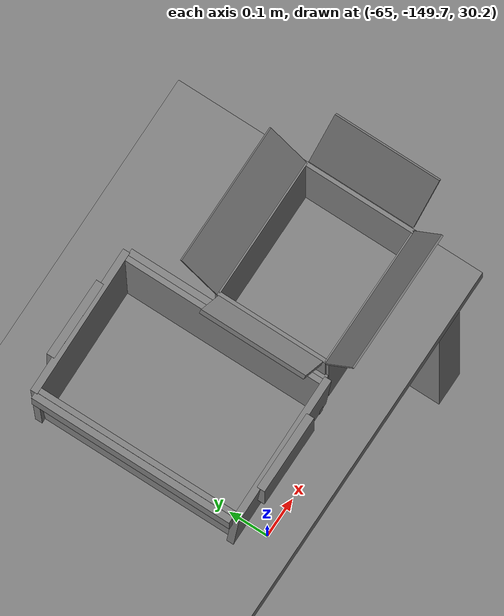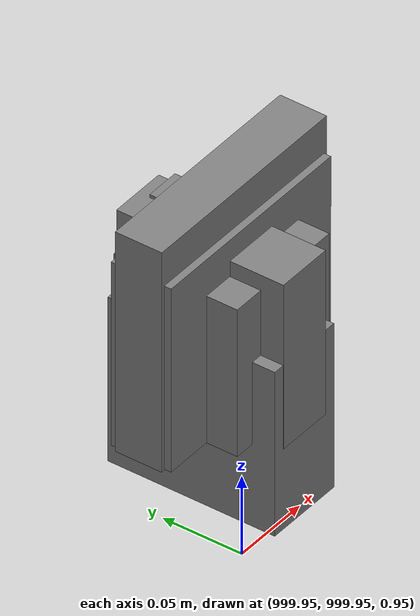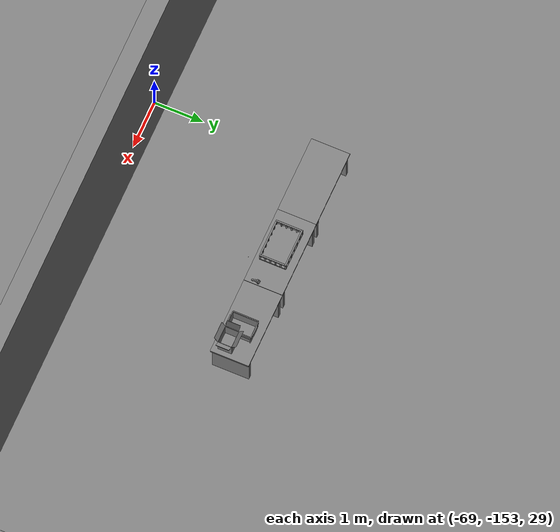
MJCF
<mujoco>
    <option gravity="0.000000000 0.000000000 -9.810000420" timestep="0.0049999999" integrator="implicitfast" density="1.225" viscosity="1.8000001e-05" noslip_iterations="10" iterations="100" sdf_iterations="50">
        <flag multiccd="disable"/>
    </option>
    <size memory="1000M"/>
    <compiler coordinate="local"/>
    <worldbody>
        <light cutoff="30" pos="0 1 1" dir="0 -1 -2"/>
        <light cutoff="30" pos="0 -1 1" dir="0 1 -2"/>
        <body pos="1000.000000000 1000.000000000 1.000000000" euler="0.000000000 0.000000000 180.000000000" name="openloong_gripper_2f85_fix_base_usda_cpu_fan">
            <geom contype="1" conaffinity="1" density="1000" type="box" material="" rgba="0.500000000 0.500000000 0.500000000 1.000000000" solimp="0.899999976 0.949999988 0.001000000" friction="1.000000000 0.005000000 0.000100000" solref="0.020000000 1.000000000" margin="0" condim="3" group="0" pos="0.000000000 0.000000000 0.070034981" quat="0.000000000 0.000000000 0.000000000 1.000000000" size="0.070700005 0.014699999 0.070700005" name="openloong_gripper_2f85_fix_base_usda_geom_CC66D3FB_4FD9_46C2_A7C3_DCEF29023744"/>
            <freejoint name="openloong_gripper_2f85_fix_base_usda_cpu_fan_joint"/>
            <site size="0.005000000 0.005000000 0.005000000" rgba="0.500000000 0.500000000 0.500000000 1.000000000" pos="0.000000000 0.000000000 0.000000000" quat="0.999961913 0.008726535 0.000000000 0.000000000" group="0" type="sphere" name="openloong_gripper_2f85_fix_base_usda_cpu_fancsite"/>
        </body>
        <body pos="1000.000000000 1000.000000000 1.000000000" euler="0.000000000 0.000000000 180.000000000" name="openloong_gripper_2f85_fix_base_usda_wifi_box">
            <geom contype="1" conaffinity="1" density="1000" type="box" material="" rgba="0.500000000 0.500000000 0.500000000 1.000000000" solimp="0.899999976 0.949999988 0.001000000" friction="1.000000000 0.005000000 0.000100000" solref="0.020000000 1.000000000" margin="0" condim="3" group="0" pos="0.000000000 0.000000000 0.058978677" quat="0.000000000 0.000000047 0.000000000 1.000000000" size="0.068499997 0.018999999 0.059000000" name="openloong_gripper_2f85_fix_base_usda_geom_920EBEF2_56DE_4C4E_9538_9E53A31F6109"/>
            <freejoint name="openloong_gripper_2f85_fix_base_usda_wifi_box_joint"/>
            <site size="0.005000000 0.005000000 0.005000000" rgba="0.500000000 0.500000000 0.500000000 1.000000000" pos="0.000000000 0.000000000 0.000000000" quat="0.999961913 0.008726500 0.000000000 0.000000000" group="0" type="sphere" name="openloong_gripper_2f85_fix_base_usda_wifi_boxsite"/>
        </body>
        <body pos="-66.062538147 -149.059371948 31.169300079" euler="-173.519317627 78.377426147 144.366744995" mocap="true" name="spotlight3_SpotLight"/>
        <body pos="-65.848182678 -149.269424438 31.171281815" euler="-50.633945465 71.953628540 -154.805023193" mocap="true" name="spotlight6_SpotLight"/>
        <body pos="1000.000000000 1000.000000000 1.000000000" euler="0.000011953 0.000005123 -179.999984741" name="openloong_gripper_2f85_fix_base_usda_intel_box">
            <geom contype="1" conaffinity="1" density="1000" type="box" material="" rgba="0.500000000 0.500000000 0.500000000 1.000000000" solimp="0.899999976 0.949999988 0.001000000" friction="1.000000000 0.005000000 0.000100000" solref="0.020000000 1.000000000" margin="0" condim="3" group="0" pos="0.000000000 -0.000067139 0.000082284" quat="0.707106709 0.000000225 0.000000253 0.707106650" size="0.052800003 0.025300000 0.052800003" name="openloong_gripper_2f85_fix_base_usda_geom_423AE73E_F9AB_4B6A_AFDD_A77AF795F849"/>
            <freejoint name="openloong_gripper_2f85_fix_base_usda_intel_box_joint"/>
            <site size="0.005000000 0.005000000 0.005000000" rgba="0.500000000 0.500000000 0.500000000 1.000000000" pos="0.000000000 0.000000000 0.000000000" quat="0.999961913 0.008726500 0.000000000 0.000000000" group="0" type="sphere" name="openloong_gripper_2f85_fix_base_usda_intel_boxsite"/>
        </body>
        <body pos="1000.000000000 999.999938965 1.000000000" euler="0.000000000 0.000000000 180.000000000" name="openloong_gripper_2f85_fix_base_usda_intelcore_i5">
            <geom contype="1" conaffinity="1" density="1000" type="box" material="" rgba="0.500000000 0.500000000 0.500000000 1.000000000" solimp="0.899999976 0.949999988 0.001000000" friction="1.000000000 0.005000000 0.000100000" solref="0.020000000 1.000000000" margin="0" condim="3" group="0" pos="0.000000000 0.000000000 0.051722717" quat="0.707106709 0.000000000 0.000000000 -0.707106769" size="0.052800000 0.018080002 0.052800000" name="openloong_gripper_2f85_fix_base_usda_geom_AED263C6_19E4_4EC3_9831_81A8EA5FBD12"/>
            <freejoint name="openloong_gripper_2f85_fix_base_usda_intelcore_i5_joint"/>
            <site size="0.005000000 0.005000000 0.005000000" rgba="0.500000000 0.500000000 0.500000000 1.000000000" pos="0.000000000 0.000000000 0.000000000" quat="0.999961913 0.008726534 0.000000000 0.000000000" group="0" type="sphere" name="openloong_gripper_2f85_fix_base_usda_intelcore_i5site"/>
        </body>
        <body pos="-66.067481995 -148.833053589 31.164930344" euler="85.945892334 -52.751438141 -73.808319092" mocap="true" name="spotlight1_SpotLight"/>
        <body pos="1000.000000000 1000.000000000 1.000000000" euler="0.000000000 0.000000000 180.000000000" name="openloong_gripper_2f85_fix_base_usda_battery_01">
            <geom contype="1" conaffinity="1" density="1000" type="box" material="" rgba="0.500000000 0.500000000 0.500000000 1.000000000" solimp="0.899999976 0.949999988 0.001000000" friction="1.000000000 0.005000000 0.000100000" solref="0.020000000 1.000000000" margin="0" condim="3" group="0" pos="-0.011123657 -0.041940309 0.101691343" quat="1.000000000 0.000000000 0.000000000 0.000000000" size="0.010800000 0.003375000 0.004725000" name="openloong_gripper_2f85_fix_base_usda_geom_72C3AEEB_F2F9_4DAA_9204_F845243092D7"/>
            <geom contype="1" conaffinity="1" density="1000" type="box" material="" rgba="0.500000000 0.500000000 0.500000000 1.000000000" solimp="0.899999976 0.949999988 0.001000000" friction="1.000000000 0.005000000 0.000100000" solref="0.020000000 1.000000000" margin="0" condim="3" group="0" pos="-0.010876465 -0.044247437 0.047066893" quat="0.998702705 -0.050920475 0.000000000 0.000000000" size="0.009450001 0.002700000 0.024975000" name="openloong_gripper_2f85_fix_base_usda_geom_8E915B82_D1F0_42B3_BEB4_4F2932FC885D"/>
            <geom contype="1" conaffinity="1" density="1000" type="box" material="" rgba="0.500000000 0.500000000 0.500000000 1.000000000" solimp="0.899999976 0.949999988 0.001000000" friction="1.000000000 0.005000000 0.000100000" solref="0.020000000 1.000000000" margin="0" condim="3" group="0" pos="-0.001235962 -0.000659180 0.047381196" quat="1.000000000 0.000000000 0.000000000 0.000000000" size="0.039420001 0.039150000 0.047250003" name="openloong_gripper_2f85_fix_base_usda_geom_34C0F172_15C8_4BF9_BD63_2A18D19F8244"/>
            <geom contype="1" conaffinity="1" density="1000" type="box" material="" rgba="0.500000000 0.500000000 0.500000000 1.000000000" solimp="0.899999976 0.949999988 0.001000000" friction="1.000000000 0.005000000 0.000100000" solref="0.020000000 1.000000000" margin="0" condim="3" group="0" pos="-0.010876465 -0.039138794 0.009851727" quat="1.000000000 0.000000000 0.000000000 0.000000000" size="0.009450001 0.010800000 0.013500000" name="openloong_gripper_2f85_fix_base_usda_geom_B41609BC_C939_461D_AA5E_69BC03ABF219"/>
            <geom contype="1" conaffinity="1" density="1000" type="box" material="" rgba="0.500000000 0.500000000 0.500000000 1.000000000" solimp="0.899999976 0.949999988 0.001000000" friction="1.000000000 0.005000000 0.000100000" solref="0.020000000 1.000000000" margin="0" condim="3" group="0" pos="-0.010876465 -0.041528322 0.071508206" quat="1.000000000 0.000000000 0.000000000 0.000000000" size="0.009450001 0.002700000 0.027000001" name="openloong_gripper_2f85_fix_base_usda_geom_5B34F002_54EB_4720_9CFB_29D86DE4DF48"/>
            <freejoint name="openloong_gripper_2f85_fix_base_usda_battery_01_joint"/>
            <site size="0.005000000 0.005000000 0.005000000" rgba="0.500000000 0.500000000 0.500000000 1.000000000" pos="0.000000000 0.000000000 0.000000000" quat="0.999961913 0.008726500 0.000000000 0.000000000" group="0" type="sphere" name="openloong_gripper_2f85_fix_base_usda_battery_01site"/>
        </body>
        <body pos="-64.866622925 -149.383972168 30.183746338" euler="89.999984741 89.999946594 0.000000000" name="openloong_gripper_2f85_fix_base_usda_bluebox_01">
            <geom contype="1" conaffinity="1" density="1000" type="box" material="" rgba="0.500000000 0.500000000 0.500000000 1.000000000" solimp="0.899999976 0.949999988 0.001000000" friction="1.000000000 0.005000000 0.000100000" solref="0.020000000 1.000000000" margin="0" condim="3" group="0" pos="0.276580811 0.187225342 0.000068665" quat="0.707106948 0.000077471 0.707106352 0.000077486" size="0.100000001 0.057999998 0.010000000" name="openloong_gripper_2f85_fix_base_usda_geom_9E19FC6B_9DB5_4B05_81D4_B071E3DD588A"/>
            <geom contype="1" conaffinity="1" density="1000" type="box" material="" rgba="0.500000000 0.500000000 0.500000000 1.000000000" solimp="0.899999976 0.949999988 0.001000000" friction="1.000000000 0.005000000 0.000100000" solref="0.020000000 1.000000000" margin="0" condim="3" group="0" pos="0.000000000 0.002883911 0.000000000" quat="0.999999881 0.000000000 0.000000000 0.000000000" size="0.254000008 0.003000000 0.172000006" name="openloong_gripper_2f85_fix_base_usda_geom_7E04B449_CB76_4C15_93D9_7366D0F0C749"/>
            <geom contype="1" conaffinity="1" density="1000" type="box" material="" rgba="0.500000000 0.500000000 0.500000000 1.000000000" solimp="0.899999976 0.949999988 0.001000000" friction="1.000000000 0.005000000 0.000100000" solref="0.020000000 1.000000000" margin="0" condim="3" group="0" pos="0.000000000 0.124874115 0.173484802" quat="0.999796331 0.020176515 -0.000000015 0.000000030" size="0.259999990 0.119999997 0.007000000" name="openloong_gripper_2f85_fix_base_usda_geom_716F0480_C9C8_4C40_84A5_57CB0B1E810F"/>
            <geom contype="1" conaffinity="1" density="1000" type="box" material="" rgba="0.500000000 0.500000000 0.500000000 1.000000000" solimp="0.899999976 0.949999988 0.001000000" friction="1.000000000 0.005000000 0.000100000" solref="0.020000000 1.000000000" margin="0" condim="3" group="0" pos="0.000000000 0.124874115 -0.173469543" quat="0.999796331 -0.020176545 -0.000000015 0.000000000" size="0.259999990 0.119999997 0.007000000" name="openloong_gripper_2f85_fix_base_usda_geom_17E377E6_24F8_4B3A_A44C_80666FC3046F"/>
            <geom contype="1" conaffinity="1" density="1000" type="box" material="" rgba="0.500000000 0.500000000 0.500000000 1.000000000" solimp="0.899999976 0.949999988 0.001000000" friction="1.000000000 0.005000000 0.000100000" solref="0.020000000 1.000000000" margin="0" condim="3" group="0" pos="0.000000000 0.214008331 0.188980103" quat="0.999912977 0.013176724 0.000000015 0.000000000" size="0.259999990 0.029999999 0.012500000" name="openloong_gripper_2f85_fix_base_usda_geom_7850313A_51A8_4CB6_A242_CADAF15F2F3C"/>
            <geom contype="1" conaffinity="1" density="1000" type="box" material="" rgba="0.500000000 0.500000000 0.500000000 1.000000000" solimp="0.899999976 0.949999988 0.001000000" friction="1.000000000 0.005000000 0.000100000" solref="0.020000000 1.000000000" margin="0" condim="3" group="0" pos="-0.258361816 0.125289917 0.001876831" quat="0.702796936 -0.020792112 0.710783124 0.020769298" size="0.189999998 0.119999997 0.009000000" name="openloong_gripper_2f85_fix_base_usda_geom_7F793F18_FF0E_4D39_B1EC_7E7E95B95DAE"/>
            <geom contype="1" conaffinity="1" density="1000" type="box" material="" rgba="0.500000000 0.500000000 0.500000000 1.000000000" solimp="0.899999976 0.949999988 0.001000000" friction="1.000000000 0.005000000 0.000100000" solref="0.020000000 1.000000000" margin="0" condim="3" group="0" pos="0.000000000 0.214008331 -0.188980103" quat="0.999912977 -0.013176769 0.000000030 0.000000015" size="0.259999990 0.029999999 0.012500000" name="openloong_gripper_2f85_fix_base_usda_geom_AF911400_2BD0_4B30_90BB_49EE7CCA50E6"/>
            <geom contype="1" conaffinity="1" density="1000" type="box" material="" rgba="0.500000000 0.500000000 0.500000000 1.000000000" solimp="0.899999976 0.949999988 0.001000000" friction="1.000000000 0.005000000 0.000100000" solref="0.020000000 1.000000000" margin="0" condim="3" group="0" pos="-0.276611328 0.187225342 0.000068665" quat="0.707106650 0.000077441 0.707106709 0.000077456" size="0.100000001 0.057999998 0.010000000" name="openloong_gripper_2f85_fix_base_usda_geom_C6852A13_8944_486B_9981_38FB61C1F9CB"/>
            <geom contype="1" conaffinity="1" density="1000" type="box" material="" rgba="0.500000000 0.500000000 0.500000000 1.000000000" solimp="0.899999976 0.949999988 0.001000000" friction="1.000000000 0.005000000 0.000100000" solref="0.020000000 1.000000000" margin="0" condim="3" group="0" pos="0.258331299 0.125289917 0.001876831" quat="0.702851415 0.018856421 0.710823774 -0.019329369" size="0.189999998 0.119999997 0.009000000" name="openloong_gripper_2f85_fix_base_usda_geom_274ADA48_DA49_4664_95C8_ED85E6BCE733"/>
            <freejoint name="openloong_gripper_2f85_fix_base_usda_bluebox_01_joint"/>
            <site size="0.005000000 0.005000000 0.005000000" rgba="0.500000000 0.500000000 0.500000000 1.000000000" pos="0.000000000 0.000000000 0.000000000" quat="0.999961913 0.008726534 0.000000000 0.000000000" group="0" type="sphere" name="openloong_gripper_2f85_fix_base_usda_bluebox_01site"/>
        </body>
        <body pos="-64.496299744 -149.491867065 30.235729218" euler="0.000000000 0.000000000 89.999946594" name="openloong_gripper_2f85_fix_base_usda_cardboardbox_01">
            <geom contype="1" conaffinity="1" density="1000" type="box" material="" rgba="0.500000000 0.500000000 0.500000000 1.000000000" solimp="0.899999976 0.949999988 0.001000000" friction="1.000000000 0.005000000 0.000100000" solref="0.020000000 1.000000000" margin="0" condim="3" group="0" pos="-0.003166199 -0.004086494 0.005052090" quat="1.000000000 0.000000000 0.000000000 0.000000000" size="0.142499998 0.177500010 0.005000000" name="openloong_gripper_2f85_fix_base_usda_geom_4BE0B898_3FA9_47A6_ACD1_EC51273E6B00"/>
            <geom contype="1" conaffinity="1" density="1000" type="box" material="" rgba="0.500000000 0.500000000 0.500000000 1.000000000" solimp="0.899999976 0.949999988 0.001000000" friction="1.000000000 0.005000000 0.000100000" solref="0.020000000 1.000000000" margin="0" condim="3" group="0" pos="-0.003166199 0.170316696 0.150570869" quat="1.000000000 0.000000000 0.000000000 0.000000000" size="0.142499998 0.005000000 0.149999991" name="openloong_gripper_2f85_fix_base_usda_geom_B257B9CD_F42A_4655_8D3F_FCEC76DC174A"/>
            <geom contype="1" conaffinity="1" density="1000" type="box" material="" rgba="0.500000000 0.500000000 0.500000000 1.000000000" solimp="0.899999976 0.949999988 0.001000000" friction="1.000000000 0.005000000 0.000100000" solref="0.020000000 1.000000000" margin="0" condim="3" group="0" pos="-0.147399902 -0.005307198 0.150570869" quat="1.000000000 0.000000000 0.000000000 0.000000000" size="0.005000000 0.177500010 0.149999991" name="openloong_gripper_2f85_fix_base_usda_geom_FF264419_8C35_41AF_8CA2_2718B109D804"/>
            <geom contype="1" conaffinity="1" density="1000" type="box" material="" rgba="0.500000000 0.500000000 0.500000000 1.000000000" solimp="0.899999976 0.949999988 0.001000000" friction="1.000000000 0.005000000 0.000100000" solref="0.020000000 1.000000000" margin="0" condim="3" group="0" pos="0.140275955 -0.005307198 0.150570869" quat="1.000000000 0.000000000 0.000000000 0.000000000" size="0.005000000 0.177500010 0.149999991" name="openloong_gripper_2f85_fix_base_usda_geom_973A0DCA_8EF8_423E_857B_1321B794069F"/>
            <geom contype="1" conaffinity="1" density="1000" type="box" material="" rgba="0.500000000 0.500000000 0.500000000 1.000000000" solimp="0.899999976 0.949999988 0.001000000" friction="1.000000000 0.005000000 0.000100000" solref="0.020000000 1.000000000" margin="0" condim="3" group="0" pos="-0.003166199 -0.181550980 0.150570869" quat="1.000000000 0.000000000 0.000000000 0.000000000" size="0.142499998 0.005000000 0.149999991" name="openloong_gripper_2f85_fix_base_usda_geom_6E7AF195_60D6_45B5_9D76_FD04445A2DAF"/>
            <freejoint name="openloong_gripper_2f85_fix_base_usda_cardboardbox_01_joint"/>
            <site size="0.005000000 0.005000000 0.005000000" rgba="0.500000000 0.500000000 0.500000000 1.000000000" pos="0.000000000 0.000000000 0.000000000" quat="0.999961913 0.008726535 0.000000000 0.000000000" group="0" type="sphere" name="openloong_gripper_2f85_fix_base_usda_site_9E9606B8_715B_426C_9FBA_1BC41E255086"/>
            <body pos="0.139160156 -0.004048347 0.301930904" euler="-179.999954224 49.383502960 179.999954224" name="openloong_gripper_2f85_fix_base_usda_A1_006">
                <geom contype="1" conaffinity="1" density="1000" type="box" material="" rgba="0.500000000 0.500000000 0.500000000 1.000000000" solimp="0.899999976 0.949999988 0.001000000" friction="1.000000000 0.005000000 0.000100000" solref="0.020000000 1.000000000" margin="0" condim="3" group="0" pos="-0.071587563 0.000009537 0.001745224" quat="0.999999881 0.000000000 0.000000000 0.000000000" size="0.071249999 0.179999992 0.002500000" name="openloong_gripper_2f85_fix_base_usda_geom_2FBC9F78_C9F5_4ED8_9C3E_ACDA15F34E19"/>
                <joint armature="0" stiffness="0.07" damping="0.0099999998" axis="0.000000 1.000000 0.000000" type="hinge" name="openloong_gripper_2f85_fix_base_usda_A1_006"/>
            </body>
            <body pos="-0.145902634 -0.004086494 0.301938057" euler="-180.000000000 -60.000011444 -180.000000000" name="openloong_gripper_2f85_fix_base_usda_A2_006">
                <geom contype="1" conaffinity="1" density="1000" type="box" material="" rgba="0.500000000 0.500000000 0.500000000 1.000000000" solimp="0.899999976 0.949999988 0.001000000" friction="1.000000000 0.005000000 0.000100000" solref="0.020000000 1.000000000" margin="0" condim="3" group="0" pos="0.071268082 0.000009537 0.002717972" quat="0.000002921 0.000000000 -0.000000030 0.999999881" size="0.071249999 0.179999992 0.002500000" name="openloong_gripper_2f85_fix_base_usda_geom_40B31F06_A402_42F7_84D7_DEB2D78C5F55"/>
                <joint armature="0" stiffness="0.07" damping="0.0099999998" axis="0.000000 1.000000 0.000000" type="hinge" name="openloong_gripper_2f85_fix_base_usda_A2_006"/>
            </body>
            <body pos="-0.003385544 0.175991058 0.301930904" euler="-125.858116150 -0.000004561 0.000002331" name="openloong_gripper_2f85_fix_base_usda_B2_006">
                <geom contype="1" conaffinity="1" density="1000" type="box" material="" rgba="0.500000000 0.500000000 0.500000000 1.000000000" solimp="0.899999976 0.949999988 0.001000000" friction="1.000000000 0.005000000 0.000100000" solref="0.020000000 1.000000000" margin="0" condim="3" group="0" pos="0.000009537 -0.070939064 -0.002470016" quat="0.999614120 0.027776197 -0.000000015 0.000000030" size="0.137500003 0.064999998 0.005000000" name="openloong_gripper_2f85_fix_base_usda_geom_39074C9E_1527_4C85_9894_B4AD5020D8CD"/>
                <joint armature="0" stiffness="0.07" damping="0.0099999998" axis="1.000000 0.000000 0.000000" type="hinge" name="openloong_gripper_2f85_fix_base_usda_B2_006"/>
            </body>
            <body pos="-0.003385544 -0.184140205 0.301938057" euler="147.805557251 0.000000000 0.000000000" name="openloong_gripper_2f85_fix_base_usda_B1_006">
                <geom contype="1" conaffinity="1" density="1000" type="box" material="" rgba="0.500000000 0.500000000 0.500000000 1.000000000" solimp="0.899999976 0.949999988 0.001000000" friction="1.000000000 0.005000000 0.000100000" solref="0.020000000 1.000000000" margin="0" condim="3" group="0" pos="-0.000028610 0.070202351 -0.002703667" quat="0.999614179 -0.027776167 0.000000000 0.000000000" size="0.137500003 0.064999998 0.005000000" name="openloong_gripper_2f85_fix_base_usda_geom_AFC2C8A9_A017_4438_A6FB_D194B99A062E"/>
                <joint armature="0" stiffness="0.07" damping="0.0099999998" axis="1.000000 0.000000 0.000000" type="hinge" name="openloong_gripper_2f85_fix_base_usda_B1_006"/>
            </body>
        </body>
        <body pos="-65.882858276 -149.481979370 30.229999542" euler="-64.487716675 0.000000000 0.000000000" name="openloong_gripper_2f85_fix_base_usda_Barcode">
            <geom contype="1" conaffinity="1" density="1000" type="box" material="" rgba="0.500000000 0.500000000 0.500000000 1.000000000" solimp="0.899999976 0.949999988 0.001000000" friction="1.000000000 0.005000000 0.000100000" solref="0.020000000 1.000000000" margin="0" condim="3" group="0" pos="0.000000000 0.013038635 0.001419067" quat="0.000000000 0.000000000 0.000000000 1.000000119" size="0.034000002 0.010000000 0.017999999" name="openloong_gripper_2f85_fix_base_usda_geom_C88FAD3F_C4DD_4F04_B8E8_9D26C3D2AD54"/>
            <geom contype="1" conaffinity="1" density="1000" type="box" material="" rgba="0.500000000 0.500000000 0.500000000 1.000000000" solimp="0.899999976 0.949999988 0.001000000" friction="1.000000000 0.005000000 0.000100000" solref="0.020000000 1.000000000" margin="0" condim="3" group="0" pos="0.000000000 -0.035301208 -0.007095337" quat="0.000000000 0.000000000 -0.043619365 0.999048233" size="0.028999999 0.010000000 0.020000000" name="openloong_gripper_2f85_fix_base_usda_geom_4E872EB7_6609_4F16_8715_554208AEF0F0"/>
            <geom contype="1" conaffinity="1" density="1000" type="box" material="" rgba="0.500000000 0.500000000 0.500000000 1.000000000" solimp="0.899999976 0.949999988 0.001000000" friction="1.000000000 0.005000000 0.000100000" solref="0.020000000 1.000000000" margin="0" condim="3" group="0" pos="0.000000000 -0.043411255 -0.011749268" quat="0.922262907 0.386563420 0.000000000 0.000000000" size="0.026000001 0.010000000 0.020000000" name="openloong_gripper_2f85_fix_base_usda_geom_32FD8D25_BAC2_4DC2_A25D_0002414C3EF9"/>
            <geom contype="1" conaffinity="1" density="1000" type="box" material="" rgba="0.500000000 0.500000000 0.500000000 1.000000000" solimp="0.899999976 0.949999988 0.001000000" friction="1.000000000 0.005000000 0.000100000" solref="0.020000000 1.000000000" margin="0" condim="3" group="0" pos="0.000000000 -0.016967773 -0.031860352" quat="0.000000000 0.000000000 0.000000000 1.000000119" size="0.008000000 0.010000000 0.013000000" name="openloong_gripper_2f85_fix_base_usda_geom_A32731B0_B6E3_4FF2_9E52_DBB5AF777771"/>
            <geom contype="1" conaffinity="1" density="1000" type="box" material="" rgba="0.500000000 0.500000000 0.500000000 1.000000000" solimp="0.899999976 0.949999988 0.001000000" friction="1.000000000 0.005000000 0.000100000" solref="0.020000000 1.000000000" margin="0" condim="3" group="0" pos="0.000000000 -0.001869202 0.000312805" quat="0.953716993 0.300705761 0.000000000 0.000000000" size="0.032000002 0.010000000 0.018999999" name="openloong_gripper_2f85_fix_base_usda_geom_496D6323_25BF_46EB_A45B_A60C7F66D0D6"/>
            <geom contype="1" conaffinity="1" density="1000" type="box" material="" rgba="0.500000000 0.500000000 0.500000000 1.000000000" solimp="0.899999976 0.949999988 0.001000000" friction="1.000000000 0.005000000 0.000100000" solref="0.020000000 1.000000000" margin="0" condim="3" group="0" pos="0.000000000 -0.019531250 -0.003173828" quat="0.953716993 0.300705761 0.000000000 0.000000000" size="0.030999999 0.010000000 0.020000000" name="openloong_gripper_2f85_fix_base_usda_geom_1A7CAD4E_930F_4EEC_894B_193458E0473E"/>
            <geom contype="1" conaffinity="1" density="1000" type="box" material="" rgba="0.500000000 0.500000000 0.500000000 1.000000000" solimp="0.899999976 0.949999988 0.001000000" friction="1.000000000 0.005000000 0.000100000" solref="0.020000000 1.000000000" margin="0" condim="3" group="0" pos="0.000000000 -0.035301208 -0.007095337" quat="0.953716993 0.300705761 0.000000000 0.000000000" size="0.028999999 0.010000000 0.020000000" name="openloong_gripper_2f85_fix_base_usda_geom_AA2C4BEA_CC71_4C52_9A22_B98DA2720525"/>
            <geom contype="1" conaffinity="1" density="1000" type="box" material="" rgba="0.500000000 0.500000000 0.500000000 1.000000000" solimp="0.899999976 0.949999988 0.001000000" friction="1.000000000 0.005000000 0.000100000" solref="0.020000000 1.000000000" margin="0" condim="3" group="0" pos="0.000000000 -0.042617798 -0.071121216" quat="0.000000000 0.000000000 0.000000000 1.000000119" size="0.013000000 0.021000000 0.059999999" name="openloong_gripper_2f85_fix_base_usda_geom_80B1F1A6_3ED0_480B_9DB2_0D5085C27D09"/>
            <freejoint name="openloong_gripper_2f85_fix_base_usda_Barcode_joint"/>
            <site size="0.005000000 0.005000000 0.005000000" rgba="0.500000000 0.500000000 0.500000000 1.000000000" pos="0.000000000 0.000000000 0.000000000" quat="1.000000000 0.000000000 0.000000000 0.000000000" group="0" type="sphere" name="openloong_gripper_2f85_fix_base_usda_Barcode_site"/>
        </body>
        <body pos="-66.745018005 -149.392349243 30.184000015" euler="0.000000000 0.000000000 89.999946594" name="[22329609642240]_Basket_01">
            <geom contype="1" conaffinity="1" density="1000" type="box" material="" rgba="0.500000000 0.500000000 0.500000000 1.000000000" solimp="0.899999976 0.949999988 0.001000000" friction="1.000000000 0.005000000 0.000100000" solref="0.020000000 1.000000000" margin="0" condim="3" group="0" pos="-0.052425385 0.389207840 0.089787483" quat="0.707107008 0.000000000 0.000000000 0.707106411" size="0.014249999 0.014249999 0.059999999" name="[22329609642240]_geom_B20CDF84_F5AA_4E71_9FEF_D11E3E7CCFD8"/>
            <geom contype="1" conaffinity="1" density="1000" type="box" material="" rgba="0.500000000 0.500000000 0.500000000 1.000000000" solimp="0.899999976 0.949999988 0.001000000" friction="1.000000000 0.005000000 0.000100000" solref="0.020000000 1.000000000" margin="0" condim="3" group="0" pos="0.264015198 -0.133043289 0.089787483" quat="0.707107008 0.000000000 0.000000000 0.707106411" size="0.014249999 0.014249999 0.059999999" name="[22329609642240]_geom_B3194F02_699E_4F89_A560_DF762537A23B"/>
            <geom contype="1" conaffinity="1" density="1000" type="box" material="" rgba="0.500000000 0.500000000 0.500000000 1.000000000" solimp="0.899999976 0.949999988 0.001000000" friction="1.000000000 0.005000000 0.000100000" solref="0.020000000 1.000000000" margin="0" condim="3" group="0" pos="-0.264015198 -0.265548706 0.089793205" quat="0.707107008 0.000000000 0.000000000 0.707106411" size="0.014249999 0.014249999 0.059999999" name="[22329609642240]_geom_5D3CC7E2_9D67_4F0A_978F_D12456BDA083"/>
            <geom contype="1" conaffinity="1" density="1000" type="box" material="" rgba="0.500000000 0.500000000 0.500000000 1.000000000" solimp="0.899999976 0.949999988 0.001000000" friction="1.000000000 0.005000000 0.000100000" solref="0.020000000 1.000000000" margin="0" condim="3" group="0" pos="-0.160263062 -0.389322281 0.089793205" quat="0.707107008 0.000000000 0.000000000 0.707106411" size="0.014249999 0.014249999 0.059999999" name="[22329609642240]_geom_92D07FEA_5E58_4035_A56D_8BDEDD08F7BB"/>
            <geom contype="1" conaffinity="1" density="1000" type="box" material="" rgba="0.500000000 0.500000000 0.500000000 1.000000000" solimp="0.899999976 0.949999988 0.001000000" friction="1.000000000 0.005000000 0.000100000" solref="0.020000000 1.000000000" margin="0" condim="3" group="0" pos="0.162265778 -0.389322281 0.089787483" quat="0.707107008 0.000000000 0.000000000 0.707106411" size="0.014249999 0.014249999 0.059999999" name="[22329609642240]_geom_0AC3B173_5F76_489F_8A70_767E37256975"/>
            <geom contype="1" conaffinity="1" density="1000" type="box" material="" rgba="0.500000000 0.500000000 0.500000000 1.000000000" solimp="0.899999976 0.949999988 0.001000000" friction="1.000000000 0.005000000 0.000100000" solref="0.020000000 1.000000000" margin="0" condim="3" group="0" pos="0.264015198 0.389207840 0.089787483" quat="0.707107008 0.000000000 0.000000000 0.707106411" size="0.014249999 0.014249999 0.059999999" name="[22329609642240]_geom_9BB61C20_B50E_4CE7_A4F8_2CB07E231CB8"/>
            <geom contype="1" conaffinity="1" density="1000" type="box" material="" rgba="0.500000000 0.500000000 0.500000000 1.000000000" solimp="0.899999976 0.949999988 0.001000000" friction="1.000000000 0.005000000 0.000100000" solref="0.020000000 1.000000000" margin="0" condim="3" group="0" pos="-0.264015198 -0.133043289 0.089793205" quat="0.707107008 0.000000000 0.000000000 0.707106411" size="0.014249999 0.014249999 0.059999999" name="[22329609642240]_geom_B47BC453_9A74_47BC_B65C_5C5B19C004C1"/>
            <geom contype="1" conaffinity="1" density="1000" type="box" material="" rgba="0.500000000 0.500000000 0.500000000 1.000000000" solimp="0.899999976 0.949999988 0.001000000" friction="1.000000000 0.005000000 0.000100000" solref="0.020000000 1.000000000" margin="0" condim="3" group="0" pos="-0.264026642 0.269256592 0.089793205" quat="0.707107008 0.000000000 0.000000000 0.707106411" size="0.014249999 0.014249999 0.059999999" name="[22329609642240]_geom_03CB2840_B2FD_4EBD_9F73_AF18930408D0"/>
            <geom contype="1" conaffinity="1" density="1000" type="box" material="" rgba="0.500000000 0.500000000 0.500000000 1.000000000" solimp="0.899999976 0.949999988 0.001000000" friction="1.000000000 0.005000000 0.000100000" solref="0.020000000 1.000000000" margin="0" condim="3" group="0" pos="0.054462433 0.389207840 0.089787483" quat="0.707107008 0.000000000 0.000000000 0.707106411" size="0.014249999 0.014249999 0.059999999" name="[22329609642240]_geom_ED2949ED_2CB6_4322_88F8_D3B717C13D9D"/>
            <geom contype="1" conaffinity="1" density="1000" type="box" material="" rgba="0.500000000 0.500000000 0.500000000 1.000000000" solimp="0.899999976 0.949999988 0.001000000" friction="1.000000000 0.005000000 0.000100000" solref="0.020000000 1.000000000" margin="0" condim="3" group="0" pos="0.054462433 -0.389322281 0.089787483" quat="0.707107008 0.000000000 0.000000000 0.707106411" size="0.014249999 0.014249999 0.059999999" name="[22329609642240]_geom_8A2A3D1A_E1B7_4CB2_BE95_5520F68B5DB2"/>
            <geom contype="1" conaffinity="1" density="1000" type="box" material="" rgba="0.500000000 0.500000000 0.500000000 1.000000000" solimp="0.899999976 0.949999988 0.001000000" friction="1.000000000 0.005000000 0.000100000" solref="0.020000000 1.000000000" margin="0" condim="3" group="0" pos="0.264015198 0.269256592 0.089793205" quat="0.707107008 0.000000000 0.000000000 0.707106411" size="0.014249999 0.014249999 0.059999999" name="[22329609642240]_geom_1928FEF9_9794_4B44_A419_168165CA5B39"/>
            <geom contype="1" conaffinity="1" density="1000" type="box" material="" rgba="0.500000000 0.500000000 0.500000000 1.000000000" solimp="0.899999976 0.949999988 0.001000000" friction="1.000000000 0.005000000 0.000100000" solref="0.020000000 1.000000000" margin="0" condim="3" group="0" pos="0.264015198 -0.389322281 0.089787483" quat="0.707107008 0.000000000 0.000000000 0.707106411" size="0.014249999 0.014249999 0.059999999" name="[22329609642240]_geom_AD70BBF9_BEAB_4CC2_BCAE_579096300155"/>
            <geom contype="1" conaffinity="1" density="1000" type="box" material="" rgba="0.500000000 0.500000000 0.500000000 1.000000000" solimp="0.899999976 0.949999988 0.001000000" friction="1.000000000 0.005000000 0.000100000" solref="0.020000000 1.000000000" margin="0" condim="3" group="0" pos="0.000000000 0.000000000 0.015998840" quat="0.707107008 0.000000000 0.000000000 0.707106411" size="0.403499991 0.279000014 0.015750000" name="[22329609642240]_geom_C24E2943_2225_49B1_B4BF_B5C6D2C6CBD4"/>
            <geom contype="1" conaffinity="1" density="1000" type="box" material="" rgba="0.500000000 0.500000000 0.500000000 1.000000000" solimp="0.899999976 0.949999988 0.001000000" friction="1.000000000 0.005000000 0.000100000" solref="0.020000000 1.000000000" margin="0" condim="3" group="0" pos="0.000000000 -0.389476776 0.163619041" quat="0.707107008 0.000000000 0.000000000 0.707106411" size="0.015000000 0.277500004 0.015750000" name="[22329609642240]_geom_9D4471F5_52E0_4615_8A0D_C78B15597218"/>
            <geom contype="1" conaffinity="1" density="1000" type="box" material="" rgba="0.500000000 0.500000000 0.500000000 1.000000000" solimp="0.899999976 0.949999988 0.001000000" friction="1.000000000 0.005000000 0.000100000" solref="0.020000000 1.000000000" margin="0" condim="3" group="0" pos="0.162265778 0.389207840 0.089787483" quat="0.707107008 0.000000000 0.000000000 0.707106411" size="0.014249999 0.014249999 0.059999999" name="[22329609642240]_geom_642ECF6B_6743_47CD_92A1_61C29A1FFAE0"/>
            <geom contype="1" conaffinity="1" density="1000" type="box" material="" rgba="0.500000000 0.500000000 0.500000000 1.000000000" solimp="0.899999976 0.949999988 0.001000000" friction="1.000000000 0.005000000 0.000100000" solref="0.020000000 1.000000000" margin="0" condim="3" group="0" pos="0.000000000 0.389471054 0.163619041" quat="0.707107008 0.000000000 0.000000000 0.707106411" size="0.015000000 0.277500004 0.015750000" name="[22329609642240]_geom_85B235FD_B753_4D84_93D9_29428A24749F"/>
            <geom contype="1" conaffinity="1" density="1000" type="box" material="" rgba="0.500000000 0.500000000 0.500000000 1.000000000" solimp="0.899999976 0.949999988 0.001000000" friction="1.000000000 0.005000000 0.000100000" solref="0.020000000 1.000000000" margin="0" condim="3" group="0" pos="-0.263511658 0.000000000 0.163619041" quat="0.707107008 0.000000000 0.000000000 0.707106411" size="0.403499991 0.015000000 0.015750000" name="[22329609642240]_geom_6EE164A2_9848_4480_AE47_AA9B93E4867C"/>
            <geom contype="1" conaffinity="1" density="1000" type="box" material="" rgba="0.500000000 0.500000000 0.500000000 1.000000000" solimp="0.899999976 0.949999988 0.001000000" friction="1.000000000 0.005000000 0.000100000" solref="0.020000000 1.000000000" margin="0" condim="3" group="0" pos="-0.264015198 0.141334534 0.089793205" quat="0.707107008 0.000000000 0.000000000 0.707106411" size="0.014249999 0.014249999 0.059999999" name="[22329609642240]_geom_5C02DAB3_0EED_4E69_B3C8_24FFF824C3B6"/>
            <geom contype="1" conaffinity="1" density="1000" type="box" material="" rgba="0.500000000 0.500000000 0.500000000 1.000000000" solimp="0.899999976 0.949999988 0.001000000" friction="1.000000000 0.005000000 0.000100000" solref="0.020000000 1.000000000" margin="0" condim="3" group="0" pos="0.264015198 -0.265548706 0.089787483" quat="0.707107008 0.000000000 0.000000000 0.707106411" size="0.014249999 0.014249999 0.059999999" name="[22329609642240]_geom_A908692F_B0F2_45BB_96E0_088C0594F5E9"/>
            <geom contype="1" conaffinity="1" density="1000" type="box" material="" rgba="0.500000000 0.500000000 0.500000000 1.000000000" solimp="0.899999976 0.949999988 0.001000000" friction="1.000000000 0.005000000 0.000100000" solref="0.020000000 1.000000000" margin="0" condim="3" group="0" pos="-0.160263062 0.389207840 0.089787483" quat="0.707107008 0.000000000 0.000000000 0.707106411" size="0.014249999 0.014249999 0.059999999" name="[22329609642240]_geom_6BB2DBB3_ED1C_4721_8DEC_004B2A545380"/>
            <geom contype="1" conaffinity="1" density="1000" type="box" material="" rgba="0.500000000 0.500000000 0.500000000 1.000000000" solimp="0.899999976 0.949999988 0.001000000" friction="1.000000000 0.005000000 0.000100000" solref="0.020000000 1.000000000" margin="0" condim="3" group="0" pos="-0.052425385 -0.389322281 0.089787483" quat="0.707107008 0.000000000 0.000000000 0.707106411" size="0.014249999 0.014249999 0.059999999" name="[22329609642240]_geom_33007219_3FF5_471B_8259_1B9C004779F1"/>
            <geom contype="1" conaffinity="1" density="1000" type="box" material="" rgba="0.500000000 0.500000000 0.500000000 1.000000000" solimp="0.899999976 0.949999988 0.001000000" friction="1.000000000 0.005000000 0.000100000" solref="0.020000000 1.000000000" margin="0" condim="3" group="0" pos="-0.264026642 -0.389322281 0.089793205" quat="0.707107008 0.000000000 0.000000000 0.707106411" size="0.014249999 0.014249999 0.059999999" name="[22329609642240]_geom_62260429_AF87_4225_B136_649C2CE914C6"/>
            <geom contype="1" conaffinity="1" density="1000" type="box" material="" rgba="0.500000000 0.500000000 0.500000000 1.000000000" solimp="0.899999976 0.949999988 0.001000000" friction="1.000000000 0.005000000 0.000100000" solref="0.020000000 1.000000000" margin="0" condim="3" group="0" pos="0.264015198 0.141334534 0.089787483" quat="0.707107008 0.000000000 0.000000000 0.707106411" size="0.014249999 0.014249999 0.059999999" name="[22329609642240]_geom_CB59BBD1_D722_4E5D_9D9B_8AECF81AB63A"/>
            <geom contype="1" conaffinity="1" density="1000" type="box" material="" rgba="0.500000000 0.500000000 0.500000000 1.000000000" solimp="0.899999976 0.949999988 0.001000000" friction="1.000000000 0.005000000 0.000100000" solref="0.020000000 1.000000000" margin="0" condim="3" group="0" pos="-0.264015198 0.389207840 0.089793205" quat="0.707107008 0.000000000 0.000000000 0.707106411" size="0.014249999 0.014249999 0.059999999" name="[22329609642240]_geom_365DBF7B_5399_4C7C_BBF2_ADA7BF1D2A31"/>
            <geom contype="1" conaffinity="1" density="1000" type="box" material="" rgba="0.500000000 0.500000000 0.500000000 1.000000000" solimp="0.899999976 0.949999988 0.001000000" friction="1.000000000 0.005000000 0.000100000" solref="0.020000000 1.000000000" margin="0" condim="3" group="0" pos="0.264015198 0.004480362 0.089787483" quat="0.707107008 0.000000000 0.000000000 0.707106411" size="0.014249999 0.014249999 0.059999999" name="[22329609642240]_geom_479B60DA_F6F7_4DEC_9A8C_746B544856B2"/>
            <geom contype="1" conaffinity="1" density="1000" type="box" material="" rgba="0.500000000 0.500000000 0.500000000 1.000000000" solimp="0.899999976 0.949999988 0.001000000" friction="1.000000000 0.005000000 0.000100000" solref="0.020000000 1.000000000" margin="0" condim="3" group="0" pos="0.263694763 -0.000011444 0.163619041" quat="0.707107008 0.000000000 0.000000000 0.707106411" size="0.403499991 0.015000000 0.015750000" name="[22329609642240]_geom_3D6CD089_EAA9_4A0E_802C_5D434B7E0C44"/>
            <geom contype="1" conaffinity="1" density="1000" type="box" material="" rgba="0.500000000 0.500000000 0.500000000 1.000000000" solimp="0.899999976 0.949999988 0.001000000" friction="1.000000000 0.005000000 0.000100000" solref="0.020000000 1.000000000" margin="0" condim="3" group="0" pos="-0.264015198 0.004480362 0.089793205" quat="0.707107008 0.000000000 0.000000000 0.707106411" size="0.014249999 0.014249999 0.059999999" name="[22329609642240]_geom_55BDD72F_E5DC_491C_BC28_C25A0C5C492A"/>
            <freejoint name="[22329609642240]_joint_726531B4_8109_469D_A644_2867922871F1"/>
        </body>
        <body pos="0.000000000 0.000000000 0.000000000" euler="0.000000000 0.000000000 0.000000000" name="Static Objects_Static Objects">
            <geom contype="1" conaffinity="1" density="1000" type="box" material="" rgba="0.500000000 0.500000000 0.500000000 1.000000000" solimp="0.899999976 0.949999988 0.001000000" friction="1.000000000 0.005000000 0.000100000" solref="0.020000000 1.000000000" margin="0" condim="3" group="0" pos="-67.544113159 -149.365814209 29.727830887" quat="0.500000417 0.499999970 0.499999553 0.499999970" size="0.381000012 0.319999993 0.041000001" name="Static Objects_geom_CC88DD4D_3E84_4523_BCFF_2A1A9806ED4F"/>
            <geom contype="1" conaffinity="1" density="1000" type="box" material="" rgba="0.500000000 0.500000000 0.500000000 1.000000000" solimp="0.899999976 0.949999988 0.001000000" friction="1.000000000 0.005000000 0.000100000" solref="0.020000000 1.000000000" margin="0" condim="3" group="0" pos="-68.239501953 -149.365814209 30.086868286" quat="0.500000417 0.499999970 0.499999553 0.499999970" size="0.370999992 0.039500002 0.745000005" name="Static Objects_geom_30EE131E_E450_450D_9536_F953F8AA3223"/>
            <geom contype="1" conaffinity="1" density="1000" type="box" material="" rgba="0.500000000 0.500000000 0.500000000 1.000000000" solimp="0.899999976 0.949999988 0.001000000" friction="1.000000000 0.005000000 0.000100000" solref="0.020000000 1.000000000" margin="0" condim="3" group="0" pos="-68.239501953 -149.365814209 30.147235870" quat="0.500000417 0.499999970 0.499999553 0.499999970" size="0.400000006 0.022000000 0.800000012" name="Static Objects_geom_6A1204F1_FFF6_41B0_9463_A8C9871D8415"/>
            <geom contype="1" conaffinity="1" density="1000" type="box" material="" rgba="0.500000000 0.500000000 0.500000000 1.000000000" solimp="0.899999976 0.949999988 0.001000000" friction="1.000000000 0.005000000 0.000100000" solref="0.020000000 1.000000000" margin="0" condim="3" group="0" pos="-68.934890747 -149.365814209 29.727830887" quat="0.500000417 0.499999970 0.499999553 0.499999970" size="0.381000012 0.319999993 0.041000001" name="Static Objects_geom_F627BE8E_2798_4EEB_80DA_556D0B81E6C2"/>
            <geom contype="1" conaffinity="1" density="1000" type="box" material="" rgba="0.500000000 0.500000000 0.500000000 1.000000000" solimp="0.899999976 0.949999988 0.001000000" friction="1.000000000 0.005000000 0.000100000" solref="0.020000000 1.000000000" margin="0" condim="3" group="0" pos="-68.239501953 -149.365814209 29.561563492" quat="0.500000417 0.499999970 0.499999553 0.499999970" size="0.020000000 0.022000000 0.660000026" name="Static Objects_geom_CA514E7C_0228_4A96_A692_A024A61ACB59"/>
            <geom contype="1" conaffinity="1" density="1000" type="box" material="" rgba="0.500000000 0.500000000 0.500000000 1.000000000" solimp="0.899999976 0.949999988 0.001000000" friction="1.000000000 0.005000000 0.000100000" solref="0.020000000 1.000000000" margin="0" condim="3" group="0" pos="-65.945671082 -149.365814209 29.727830887" quat="0.500000417 0.499999970 0.499999553 0.499999970" size="0.381000012 0.319999993 0.041000001" name="Static Objects_geom_5FC2651B_4410_4DB4_87C7_6289E7F1ADF3"/>
            <geom contype="1" conaffinity="1" density="1000" type="box" material="" rgba="0.500000000 0.500000000 0.500000000 1.000000000" solimp="0.899999976 0.949999988 0.001000000" friction="1.000000000 0.005000000 0.000100000" solref="0.020000000 1.000000000" margin="0" condim="3" group="0" pos="-66.641059875 -149.365814209 30.086868286" quat="0.500000417 0.499999970 0.499999553 0.499999970" size="0.370999992 0.039500002 0.745000005" name="Static Objects_geom_113AF744_AEE4_4D2C_B631_C0DAE3E0D726"/>
            <geom contype="1" conaffinity="1" density="1000" type="box" material="" rgba="0.500000000 0.500000000 0.500000000 1.000000000" solimp="0.899999976 0.949999988 0.001000000" friction="1.000000000 0.005000000 0.000100000" solref="0.020000000 1.000000000" margin="0" condim="3" group="0" pos="-66.641059875 -149.365814209 30.147235870" quat="0.500000417 0.499999970 0.499999553 0.499999970" size="0.400000006 0.022000000 0.800000012" name="Static Objects_geom_51F4F1F4_D4C6_4C4C_BF5F_E2CDF45F7F26"/>
            <geom contype="1" conaffinity="1" density="1000" type="box" material="" rgba="0.500000000 0.500000000 0.500000000 1.000000000" solimp="0.899999976 0.949999988 0.001000000" friction="1.000000000 0.005000000 0.000100000" solref="0.020000000 1.000000000" margin="0" condim="3" group="0" pos="-67.336448669 -149.365814209 29.727830887" quat="0.500000417 0.499999970 0.499999553 0.499999970" size="0.381000012 0.319999993 0.041000001" name="Static Objects_geom_4E5FCE07_4B89_4184_9522_2C7ACAE0F1B7"/>
            <geom contype="1" conaffinity="1" density="1000" type="box" material="" rgba="0.500000000 0.500000000 0.500000000 1.000000000" solimp="0.899999976 0.949999988 0.001000000" friction="1.000000000 0.005000000 0.000100000" solref="0.020000000 1.000000000" margin="0" condim="3" group="0" pos="-66.641059875 -149.365814209 29.561563492" quat="0.500000417 0.499999970 0.499999553 0.499999970" size="0.020000000 0.022000000 0.660000026" name="Static Objects_geom_72EE815E_309E_4EA0_B918_B5F3C8639356"/>
            <geom contype="1" conaffinity="1" density="1000" type="box" material="" rgba="0.500000000 0.500000000 0.500000000 1.000000000" solimp="0.899999976 0.949999988 0.001000000" friction="1.000000000 0.005000000 0.000100000" solref="0.020000000 1.000000000" margin="0" condim="3" group="0" pos="-64.338577271 -149.365814209 29.727830887" quat="0.500000417 0.499999970 0.499999553 0.499999970" size="0.381000012 0.319999993 0.041000001" name="Static Objects_geom_14FDF7B2_FD36_4868_842C_A37E07008917"/>
            <geom contype="1" conaffinity="1" density="1000" type="box" material="" rgba="0.500000000 0.500000000 0.500000000 1.000000000" solimp="0.899999976 0.949999988 0.001000000" friction="1.000000000 0.005000000 0.000100000" solref="0.020000000 1.000000000" margin="0" condim="3" group="0" pos="-65.033966064 -149.365814209 30.086868286" quat="0.500000417 0.499999970 0.499999553 0.499999970" size="0.370999992 0.039500002 0.745000005" name="Static Objects_geom_F2DFB25C_B396_4485_849F_F05394DDACBB"/>
            <geom contype="1" conaffinity="1" density="1000" type="box" material="" rgba="0.500000000 0.500000000 0.500000000 1.000000000" solimp="0.899999976 0.949999988 0.001000000" friction="1.000000000 0.005000000 0.000100000" solref="0.020000000 1.000000000" margin="0" condim="3" group="0" pos="-65.033966064 -149.365814209 30.147235870" quat="0.500000417 0.499999970 0.499999553 0.499999970" size="0.400000006 0.022000000 0.800000012" name="Static Objects_geom_866F5913_A9BF_42ED_8F4A_C0E9339A08E6"/>
            <geom contype="1" conaffinity="1" density="1000" type="box" material="" rgba="0.500000000 0.500000000 0.500000000 1.000000000" solimp="0.899999976 0.949999988 0.001000000" friction="1.000000000 0.005000000 0.000100000" solref="0.020000000 1.000000000" margin="0" condim="3" group="0" pos="-65.729354858 -149.365814209 29.727830887" quat="0.500000417 0.499999970 0.499999553 0.499999970" size="0.381000012 0.319999993 0.041000001" name="Static Objects_geom_367CD053_32C2_4F36_8833_A154E5042B0B"/>
            <geom contype="1" conaffinity="1" density="1000" type="box" material="" rgba="0.500000000 0.500000000 0.500000000 1.000000000" solimp="0.899999976 0.949999988 0.001000000" friction="1.000000000 0.005000000 0.000100000" solref="0.020000000 1.000000000" margin="0" condim="3" group="0" pos="-65.033966064 -149.365814209 29.561563492" quat="0.500000417 0.499999970 0.499999553 0.499999970" size="0.020000000 0.022000000 0.660000026" name="Static Objects_geom_73F0A9C5_E7CB_4617_8FEC_302D12B3046B"/>
            <geom contype="1" conaffinity="1" density="1000" type="box" material="" rgba="0.500000000 0.500000000 0.500000000 1.000000000" solimp="0.899999976 0.949999988 0.001000000" friction="1.000000000 0.005000000 0.000100000" solref="0.020000000 1.000000000" margin="0" condim="3" group="0" pos="-61.754566193 -137.853729248 33.906845093" quat="0.707107067 0.000000000 0.000000000 0.707106471" size="0.759999990 0.759999990 4.500000000" name="Static Objects_geom_3538A0D0_A470_43A8_ACBB_3596A835AE9F"/>
            <geom contype="1" conaffinity="1" density="1000" type="box" material="" rgba="0.500000000 0.500000000 0.500000000 1.000000000" solimp="0.899999976 0.949999988 0.001000000" friction="1.000000000 0.005000000 0.000100000" solref="0.020000000 1.000000000" margin="0" condim="3" group="0" pos="-57.511135101 -144.927108765 31.707921982" quat="1.000000000 0.000000000 0.000000000 0.000000000" size="0.200000003 8.000000000 2.299999952" name="Static Objects_geom_5005A52D_3ADA_44AE_AE7D_EAD9EE7CBB7A"/>
            <geom contype="1" conaffinity="1" density="1000" type="box" material="" rgba="0.500000000 0.500000000 0.500000000 1.000000000" solimp="0.899999976 0.949999988 0.001000000" friction="1.000000000 0.005000000 0.000100000" solref="0.020000000 1.000000000" margin="0" condim="3" group="0" pos="-80.517646790 -157.574050903 31.688196182" quat="0.707107067 0.000000000 0.000000000 0.707106471" size="0.600000024 0.600000024 2.299999952" name="Static Objects_geom_D65E7CD0_FEC7_4CE7_B7D2_0C5FC97AA14C"/>
            <geom contype="1" conaffinity="1" density="1000" type="box" material="" rgba="0.500000000 0.500000000 0.500000000 1.000000000" solimp="0.899999976 0.949999988 0.001000000" friction="1.000000000 0.005000000 0.000100000" solref="0.020000000 1.000000000" margin="0" condim="3" group="0" pos="-80.711044312 -147.414932251 31.666158676" quat="1.000000000 0.000000000 0.000000000 0.000000000" size="0.200000003 10.000000000 2.299999952" name="Static Objects_geom_8849A81B_67FE_43BD_A969_12261CBE6515"/>
            <geom contype="1" conaffinity="1" density="1000" type="box" material="" rgba="0.500000000 0.500000000 0.500000000 1.000000000" solimp="0.899999976 0.949999988 0.001000000" friction="1.000000000 0.005000000 0.000100000" solref="0.020000000 1.000000000" margin="0" condim="3" group="0" pos="-57.687217712 -137.434692383 31.688196182" quat="0.707107067 0.000000000 0.000000000 0.707106471" size="0.600000024 0.600000024 2.299999952" name="Static Objects_geom_69D2EBB8_7FE7_46EA_954C_7833B7E6703E"/>
            <geom contype="1" conaffinity="1" density="1000" type="box" material="" rgba="0.500000000 0.500000000 0.500000000 1.000000000" solimp="0.899999976 0.949999988 0.001000000" friction="1.000000000 0.005000000 0.000100000" solref="0.020000000 1.000000000" margin="0" condim="3" group="0" pos="-69.537033081 -140.263229370 31.714921951" quat="0.707107067 0.000000000 0.000000000 0.707106471" size="0.759999990 4.500000000 2.299999952" name="Static Objects_geom_8E4C4661_ED4B_4B62_9236_B546C63EDFE9"/>
            <geom contype="1" conaffinity="1" density="1000" type="box" material="" rgba="0.500000000 0.500000000 0.500000000 1.000000000" solimp="0.899999976 0.949999988 0.001000000" friction="1.000000000 0.005000000 0.000100000" solref="0.020000000 1.000000000" margin="0" condim="3" group="0" pos="-80.073638916 -137.853713989 33.906845093" quat="0.707107067 0.000000000 0.000000000 0.707106471" size="0.759999990 0.759999990 4.500000000" name="Static Objects_geom_6D73CF1D_6CF1_422B_B0B3_BF1833F9943C"/>
            <geom contype="1" conaffinity="1" density="1000" type="box" material="" rgba="0.500000000 0.500000000 0.500000000 1.000000000" solimp="0.899999976 0.949999988 0.001000000" friction="1.000000000 0.005000000 0.000100000" solref="0.020000000 1.000000000" margin="0" condim="3" group="0" pos="-73.406707764 -155.734664917 31.707921982" quat="1.000000000 0.000000000 0.000000000 0.000000000" size="0.200000003 3.000000000 2.299999952" name="Static Objects_geom_55E61547_EEB6_4B2A_BB39_D6F0663E2230"/>
            <geom contype="1" conaffinity="1" density="1000" type="box" material="" rgba="0.500000000 0.500000000 0.500000000 1.000000000" solimp="0.899999976 0.949999988 0.001000000" friction="1.000000000 0.005000000 0.000100000" solref="0.020000000 1.000000000" margin="0" condim="3" group="0" pos="-68.497543335 -137.448257446 31.707921982" quat="0.707107067 0.000000000 0.000000000 0.707106471" size="0.200000003 14.000000000 2.299999952" name="Static Objects_geom_32072480_9DE9_44A6_AC59_D9940F2515B0"/>
            <geom contype="1" conaffinity="1" density="1000" type="cylinder" material="" rgba="0.500000000 0.500000000 0.500000000 1.000000000" solimp="0.899999976 0.949999988 0.001000000" friction="1.000000000 0.005000000 0.000100000" solref="0.020000000 1.000000000" margin="0" condim="3" group="0" pos="-68.868522644 -142.134506226 31.711090088" quat="0.707107067 0.000000000 0.000000000 0.707106471" size="0.509999990 2.299999952 1.000000000" name="Static Objects_geom_CAF6ED74_E65E_44BD_B0AE_0476CA877F61"/>
            <geom contype="1" conaffinity="1" density="1000" type="plane" material="" rgba="0.500000000 0.500000000 0.500000000 1.000000000" solimp="0.899999976 0.949999988 0.001000000" friction="1.000000000 0.005000000 0.000100000" solref="0.020000000 1.000000000" margin="0" condim="3" group="0" pos="-72.873703003 -147.131927490 29.409669876" quat="1.000000000 0.000000000 0.000000000 0.000000000" size="18.000000000 14.000000000 1.000000000" name="Static Objects_geom_26B07173_C2D6_4C96_8037_EE7AA906F1D2"/>
            <geom contype="1" conaffinity="1" density="1000" type="box" material="" rgba="0.500000000 0.500000000 0.500000000 1.000000000" solimp="0.899999976 0.949999988 0.001000000" friction="1.000000000 0.005000000 0.000100000" solref="0.020000000 1.000000000" margin="0" condim="3" group="0" pos="-79.943580627 -157.782272339 31.707921982" quat="0.707107067 0.000000000 0.000000000 0.707106471" size="0.200000003 7.000000000 2.299999952" name="Static Objects_geom_3E78F6DA_6B4D_4729_BDD1_C3C03FC376C2"/>
            <geom contype="1" conaffinity="1" density="1000" type="box" material="" rgba="0.500000000 0.500000000 0.500000000 1.000000000" solimp="0.899999976 0.949999988 0.001000000" friction="1.000000000 0.005000000 0.000100000" solref="0.020000000 1.000000000" margin="0" condim="3" group="0" pos="-65.421028137 -152.903442383 31.707921982" quat="0.707107067 0.000000000 0.000000000 0.707106471" size="0.200000003 7.800000191 2.299999952" name="Static Objects_geom_36E0EDC4_84F3_4A9D_94D4_0A97798BACFA"/>
            <geom contype="1" conaffinity="1" density="1000" type="box" material="" rgba="0.500000000 0.500000000 0.500000000 1.000000000" solimp="0.899999976 0.949999988 0.001000000" friction="1.000000000 0.005000000 0.000100000" solref="0.020000000 1.000000000" margin="0" condim="3" group="0" pos="-74.776908875 -149.964416504 31.688196182" quat="1.000000000 0.000000000 0.000000000 0.000000000" size="0.600000024 0.409999996 2.299999952" name="Static Objects_geom_36167EFD_C08B_41E0_B61D_A769A0053E8C"/>
            <geom contype="1" conaffinity="1" density="1000" type="cylinder" material="" rgba="0.500000000 0.500000000 0.500000000 1.000000000" solimp="0.899999976 0.949999988 0.001000000" friction="1.000000000 0.005000000 0.000100000" solref="0.020000000 1.000000000" margin="0" condim="3" group="0" pos="-60.161884308 -142.134506226 31.711090088" quat="0.707107067 0.000000000 0.000000000 0.707106471" size="0.509999990 2.299999952 1.000000000" name="Static Objects_geom_11B39A8E_9B58_48E2_A66E_BAEFE87E82D1"/>
            <geom contype="1" conaffinity="1" density="1000" type="cylinder" material="" rgba="0.500000000 0.500000000 0.500000000 1.000000000" solimp="0.899999976 0.949999988 0.001000000" friction="1.000000000 0.005000000 0.000100000" solref="0.020000000 1.000000000" margin="0" condim="3" group="0" pos="-75.382453918 -149.963455200 31.711090088" quat="0.707107067 0.000000000 0.000000000 0.707106471" size="0.409999996 2.299999952 1.000000000" name="Static Objects_geom_FB320EDC_17DF_4F03_AE76_13EF90D2BE72"/>
            <geom contype="1" conaffinity="1" density="1000" type="cylinder" material="" rgba="0.500000000 0.500000000 0.500000000 1.000000000" solimp="0.899999976 0.949999988 0.001000000" friction="1.000000000 0.005000000 0.000100000" solref="0.020000000 1.000000000" margin="0" condim="3" group="0" pos="-74.154960632 -149.963455200 31.711090088" quat="0.707107067 0.000000000 0.000000000 0.707106471" size="0.409999996 2.299999952 1.000000000" name="Static Objects_geom_02DBB1A2_2E71_4785_BA51_4FD0F2E680D9"/>
            <geom contype="1" conaffinity="1" density="1000" type="cylinder" material="" rgba="0.500000000 0.500000000 0.500000000 1.000000000" solimp="0.899999976 0.949999988 0.001000000" friction="1.000000000 0.005000000 0.000100000" solref="0.020000000 1.000000000" margin="0" condim="3" group="0" pos="-77.566612244 -142.134506226 31.711090088" quat="0.707107067 0.000000000 0.000000000 0.707106471" size="0.509999990 2.299999952 1.000000000" name="Static Objects_geom_08CF559F_BDDE_41D7_BC07_A199094AA23B"/>
        </body>
        <body pos="-66.291030884 -149.869689941 29.018842697" euler="0.000000000 0.000000000 89.999946594" mocap="true" name="openloong_gripper_2f85_fix_base_usda_leftHandMocap"/>
        <body pos="-66.291030884 -149.869689941 29.018842697" euler="0.000000000 0.000000000 89.999946594" mocap="true" name="openloong_gripper_2f85_fix_base_usda_rightHandMocap"/>
        <body pos="-66.291030884 -149.869689941 30.218843460" euler="0.000000000 0.000000000 89.999946594" name="openloong_gripper_2f85_fix_base_usda_base_link">
            <geom contype="1" conaffinity="1" density="1000" type="mesh" material="" rgba="0.783999979 0.783999979 0.783999979 1.000000000" solimp="0.899999976 0.949999988 0.001000000" friction="1.000000000 0.005000000 0.000100000" solref="0.020000000 1.000000000" margin="0" condim="3" group="3" mesh="base_link" pos="0.000000000 0.000000000 0.000000000" quat="1.000000000 0.000000000 0.000000000 0.000000000" size="1.000000000 1.000000000 1.000000000" name="openloong_gripper_2f85_fix_base_usda__geom_7_A22348F7_1269_4745_A21D_33AE74641C43"/>
            <site size="0.005000000 0.005000000 0.005000000" rgba="0.500000000 0.500000000 0.500000000 1.000000000" pos="0.000000000 0.000000000 0.000000000" quat="1.000000000 0.000000000 0.000000000 0.000000000" group="0" type="sphere" name="openloong_gripper_2f85_fix_base_usda_imu"/>
            <inertial mass="22.447001" pos="-0.005664100 -0.001336700 0.238289997" diaginertia="0.374352545 0.277180195 0.220617250" quat="0.999247074 0.035235517 -0.015086859 0.006023135"/>
            <body pos="0.000000000 0.000000000 0.299997330" euler="0.000000000 0.000000000 0.000000000" name="openloong_gripper_2f85_fix_base_usda_dummy_body">
                <geom contype="1" conaffinity="1" density="1000" type="sphere" material="" rgba="0.783999979 0.783999979 0.783999979 1.000000000" solimp="0.899999976 0.949999988 0.001000000" friction="1.000000000 0.005000000 0.000100000" solref="0.020000000 1.000000000" margin="0" condim="3" group="3" pos="0.000000000 0.000000000 0.000000000" quat="1.000000000 0.000000000 0.000000000 0.000000000" size="0.010000000 0.000000000 0.000000000" name="openloong_gripper_2f85_fix_base_usda__geom_8_9ACC23F2_C7AD_4592_9966_A1A9B490C6C7"/>
                <joint armature="0.0099999998" stiffness="0" damping="0.1" axis="0.000000 0.000000 1.000000" type="hinge" name="openloong_gripper_2f85_fix_base_usda_dummy_joint"/>
                <site size="0.010000000 0.005000000 0.005000000" rgba="0.500000000 0.500000000 0.500000000 1.000000000" pos="0.000000000 0.000000000 0.000000000" quat="1.000000000 0.000000000 0.000000000 0.000000000" group="3" type="sphere" name="openloong_gripper_2f85_fix_base_usda_dummy_site"/>
            </body>
            <body pos="0.009002686 0.000000000 0.406400681" euler="0.000000000 0.000000000 0.000000000" name="openloong_gripper_2f85_fix_base_usda_Link_head_yaw">
                <geom contype="1" conaffinity="1" density="1000" type="mesh" material="" rgba="0.783999979 0.783999979 0.783999979 1.000000000" solimp="0.899999976 0.949999988 0.001000000" friction="1.000000000 0.005000000 0.000100000" solref="0.020000000 1.000000000" margin="0" condim="3" group="3" mesh="Link_head_yaw" pos="0.000000000 0.000000000 0.000000000" quat="1.000000000 0.000000000 0.000000000 0.000000000" size="1.000000000 1.000000000 1.000000000" name="openloong_gripper_2f85_fix_base_usda__geom_10_51606363_A80F_4612_8DD0_C8AF872F7490"/>
                <inertial mass="0.84249002" pos="0.000000000 -0.002081400 0.044801001" diaginertia="0.000700588 0.000629000 0.000553812" quat="0.706933022 -0.015675601 0.015677100 0.706933022"/>
                <body pos="0.000000000 -0.034599304 0.048500061" euler="0.000000000 0.000000000 0.000000000" name="openloong_gripper_2f85_fix_base_usda_Link_head_pitch">
                    <geom contype="1" conaffinity="1" density="1000" type="mesh" material="" rgba="0.783999979 0.783999979 0.783999979 1.000000000" solimp="0.899999976 0.949999988 0.001000000" friction="1.000000000 0.005000000 0.000100000" solref="0.020000000 1.000000000" margin="0" condim="3" group="3" mesh="Link_head_pitch" pos="0.000000000 0.000000000 0.000000000" quat="1.000000000 0.000000000 0.000000000 0.000000000" size="1.000000000 1.000000000 1.000000000" name="openloong_gripper_2f85_fix_base_usda__geom_12_B765C884_BC5D_4D3B_99D3_2B8260767D8A"/>
                    <inertial mass="1.3943" pos="0.020569000 0.033004001 0.125000000" diaginertia="0.006381400 0.006289940 0.004481460" quat="0.973390222 0.008406822 0.228157058 0.019624906"/>
                    <body pos="0.000000000 0.029998779 0.000000000" euler="0.000000000 0.000000000 0.000000000" name="openloong_gripper_2f85_fix_base_usda_neck_center_body">
                        <site size="0.010000000 0.005000000 0.005000000" rgba="0.500000000 0.500000000 0.500000000 1.000000000" pos="0.000000000 0.000000000 0.000000000" quat="1.000000000 0.000000000 0.000000000 0.000000000" group="3" type="sphere" name="openloong_gripper_2f85_fix_base_usda_neck_center_site"/>
                        <body pos="0.020004272 0.000000000 0.149999619" euler="-0.000002229 39.998176575 -90.000205994" name="openloong_gripper_2f85_fix_base_usda_camera_head">
                            <site size="0.010000000 0.005000000 0.005000000" rgba="0.500000000 0.500000000 0.500000000 1.000000000" pos="0.000000000 0.000000000 0.000000000" quat="1.000000000 0.000000000 0.000000000 0.000000000" group="3" type="sphere" name="openloong_gripper_2f85_fix_base_usda_camera_head_site"/>
                        </body>
                    </body>
                </body>
            </body>
            <body pos="0.003997803 -0.161598206 0.392200470" euler="0.000000000 0.000000000 0.000000000" name="openloong_gripper_2f85_fix_base_usda_Link_arm_r_01">
                <geom contype="1" conaffinity="1" density="1000" type="mesh" material="" rgba="0.783999979 0.783999979 0.783999979 1.000000000" solimp="0.899999976 0.949999988 0.001000000" friction="1.000000000 0.005000000 0.000100000" solref="0.020000000 1.000000000" margin="0" condim="3" group="3" mesh="Link_arm_r_01" pos="0.000000000 0.000000000 0.000000000" quat="1.000000000 0.000000000 0.000000000 0.000000000" size="1.000000000 1.000000000 1.000000000" name="openloong_gripper_2f85_fix_base_usda__geom_14_9C6FC42D_05A7_43E1_84DC_5941EA08144A"/>
                <joint armature="0.0099999998" stiffness="0" damping="1" axis="0.000000 -1.000000 0.000000" limited="true" range="-170.000015259 170.000015259" type="hinge" name="openloong_gripper_2f85_fix_base_usda_J_arm_r_01"/>
                <inertial mass="0.75641" pos="0.004494600 -0.038293999 -0.000001874" diaginertia="0.000842990 0.000803050 0.000587120" quat="-0.000163502 0.707098067 0.000812463 0.707115054"/>
                <body pos="-0.041992188 -0.041000366 0.000000000" euler="0.000000000 0.000000000 0.000000000" name="openloong_gripper_2f85_fix_base_usda_Link_arm_r_02">
                    <geom contype="1" conaffinity="1" density="1000" type="mesh" material="" rgba="0.783999979 0.783999979 0.783999979 1.000000000" solimp="0.899999976 0.949999988 0.001000000" friction="1.000000000 0.005000000 0.000100000" solref="0.020000000 1.000000000" margin="0" condim="3" group="3" mesh="Link_arm_r_02" pos="0.000000000 0.000000000 0.000000000" quat="1.000000000 0.000000000 0.000000000 0.000000000" size="1.000000000 1.000000000 1.000000000" name="openloong_gripper_2f85_fix_base_usda__geom_16_D076332B_4ECB_493C_B6C3_C252013E4D60"/>
                    <joint armature="0.0099999998" stiffness="0" damping="1" axis="-1.000000 0.000000 0.000000" limited="true" range="-105.000244141 105.000244141" type="hinge" name="openloong_gripper_2f85_fix_base_usda_J_arm_r_02"/>
                    <inertial mass="0.98500001" pos="0.041999999 -0.067430697 0.000000000" diaginertia="0.002262690 0.001730990 0.001154020" quat="0.500000000 0.500000000 -0.500000000 0.500000000"/>
                    <body pos="0.041992188 -0.122596741 0.000000000" euler="0.000000000 0.000000000 0.000000000" name="openloong_gripper_2f85_fix_base_usda_Link_arm_r_03">
                        <geom contype="1" conaffinity="1" density="1000" type="mesh" material="" rgba="0.783999979 0.783999979 0.783999979 1.000000000" solimp="0.899999976 0.949999988 0.001000000" friction="1.000000000 0.005000000 0.000100000" solref="0.020000000 1.000000000" margin="0" condim="3" group="3" mesh="Link_arm_r_03" pos="0.000000000 0.000000000 0.000000000" quat="1.000000000 0.000000000 0.000000000 0.000000000" size="1.000000000 1.000000000 1.000000000" name="openloong_gripper_2f85_fix_base_usda__geom_18_E39FDC74_2526_4E89_BEDF_DC094762B33F"/>
                        <joint armature="0.0099999998" stiffness="0" damping="1" axis="0.000000 -1.000000 0.000000" limited="true" range="-170.000015259 170.000015259" type="hinge" name="openloong_gripper_2f85_fix_base_usda_J_arm_r_03"/>
                        <inertial mass="0.95899999" pos="-0.001413580 -0.164663002 0.020757901" diaginertia="0.002101340 0.002064590 0.000754802" quat="0.560480952 0.454391927 -0.443732947 0.531497955"/>
                        <body pos="0.035293579 -0.177406311 0.023998260" euler="0.000000000 0.000000000 0.000000000" name="openloong_gripper_2f85_fix_base_usda_Link_arm_r_04">
                            <geom contype="1" conaffinity="1" density="1000" type="mesh" material="" rgba="0.783999979 0.783999979 0.783999979 1.000000000" solimp="0.899999976 0.949999988 0.001000000" friction="1.000000000 0.005000000 0.000100000" solref="0.020000000 1.000000000" margin="0" condim="3" group="3" mesh="Link_arm_r_04" pos="0.000000000 0.000000000 0.000000000" quat="1.000000000 0.000000000 0.000000000 0.000000000" size="1.000000000 1.000000000 1.000000000" name="openloong_gripper_2f85_fix_base_usda__geom_20_4D501138_0E9F_4A7F_A031_6C4A35A4C39A"/>
                            <joint armature="0.0099999998" stiffness="0" damping="1" axis="-1.000000 0.000000 0.000000" limited="true" range="0.000000000 170.000015259" type="hinge" name="openloong_gripper_2f85_fix_base_usda_J_arm_r_04"/>
                            <inertial mass="0.60000002" pos="-0.038727000 -0.060766999 -0.021003000" diaginertia="0.001092610 0.000712422 0.000645102" quat="0.327701002 0.632602990 -0.467366993 0.523443997"/>
                            <body pos="-0.035293579 -0.103492737 -0.023998260" euler="0.000000000 0.000000000 0.000000000" name="openloong_gripper_2f85_fix_base_usda_Link_arm_r_05">
                                <geom contype="1" conaffinity="1" density="1000" type="mesh" material="" rgba="0.783999979 0.783999979 0.783999979 1.000000000" solimp="0.899999976 0.949999988 0.001000000" friction="1.000000000 0.005000000 0.000100000" solref="0.020000000 1.000000000" margin="0" condim="3" group="3" mesh="Link_arm_r_05" pos="0.000000000 0.000000000 0.000000000" quat="1.000000000 0.000000000 0.000000000 0.000000000" size="1.000000000 1.000000000 1.000000000" name="openloong_gripper_2f85_fix_base_usda__geom_22_A3AC3810_CD7E_43E3_9BAC_53F894B5D165"/>
                                <joint armature="0.0099999998" stiffness="0" damping="1" axis="0.000000 -1.000000 0.000000" limited="true" range="-170.000015259 170.000015259" type="hinge" name="openloong_gripper_2f85_fix_base_usda_J_arm_r_05"/>
                                <inertial mass="0.68976003" pos="0.000032712 -0.068658002 -0.000111780" diaginertia="0.002522510 0.002411100 0.000448695" quat="0.707660973 0.706543028 -0.002603360 0.002470550"/>
                                <body pos="-0.026489258 -0.196502686 0.000000000" euler="0.000000000 0.000000000 0.000000000" name="openloong_gripper_2f85_fix_base_usda_Link_arm_r_06">
                                    <geom contype="1" conaffinity="1" density="1000" type="mesh" material="" rgba="0.783999979 0.783999979 0.783999979 1.000000000" solimp="0.899999976 0.949999988 0.001000000" friction="1.000000000 0.005000000 0.000100000" solref="0.020000000 1.000000000" margin="0" condim="3" group="3" mesh="Link_arm_r_06" pos="0.000000000 0.000000000 0.000000000" quat="1.000000000 0.000000000 0.000000000 0.000000000" size="1.000000000 1.000000000 1.000000000" name="openloong_gripper_2f85_fix_base_usda__geom_24_08D06CB2_6620_452D_A351_DA8013C1BAA8"/>
                                    <joint armature="0.0099999998" stiffness="0" damping="1" axis="1.000000 0.000000 0.000000" limited="true" range="-105.000244141 105.000244141" type="hinge" name="openloong_gripper_2f85_fix_base_usda_J_arm_r_06"/>
                                    <inertial mass="0.28" pos="0.026078001 -0.000000896 0.001663700" diaginertia="0.000156930 0.000145601 0.000104979" quat="0.707080841 0.001851080 0.001883810 0.707127810"/>
                                    <body pos="0.026489258 0.000000000 0.031799316" euler="0.000000000 0.000000000 0.000000000" name="openloong_gripper_2f85_fix_base_usda_Link_arm_r_07">
                                        <geom contype="1" conaffinity="1" density="1000" type="mesh" material="" rgba="0.783999979 0.783999979 0.783999979 1.000000000" solimp="0.899999976 0.949999988 0.001000000" friction="1.000000000 0.005000000 0.000100000" solref="0.020000000 1.000000000" margin="0" condim="3" group="3" mesh="Link_arm_r_07" pos="0.000000000 0.000000000 0.000000000" quat="1.000000000 0.000000000 0.000000000 0.000000000" size="1.000000000 1.000000000 1.000000000" name="openloong_gripper_2f85_fix_base_usda__geom_26_EC16E40D_DF53_43AB_A24C_4357C2A06C8B"/>
                                        <joint armature="0.0099999998" stiffness="0" damping="1" axis="0.000000 0.000000 1.000000" limited="true" range="-60.000133514 60.000133514" type="hinge" name="openloong_gripper_2f85_fix_base_usda_J_arm_r_07"/>
                                        <inertial mass="0.61353999" pos="-0.007859000 -0.158170000 -0.027736001" diaginertia="0.003037610 0.002570910 0.000729379" quat="0.427542925 0.443532884 -0.553093910 0.560867906"/>
                                        <body pos="0.000000000 0.286994934 -0.270000458" euler="150.000350952 -0.000001649 -0.000000442" name="openloong_gripper_2f85_fix_base_usda_camera_wrist_r">
                                            <site size="0.010000000 0.005000000 0.005000000" rgba="0.500000000 0.500000000 0.500000000 1.000000000" pos="0.000000000 0.000000000 0.000000000" quat="1.000000000 0.000000000 0.000000000 0.000000000" group="3" type="sphere" name="openloong_gripper_2f85_fix_base_usda_camera_wrist_r_site"/>
                                        </body>
                                        <body pos="0.000000000 -0.220008850 -0.033002853" euler="0.000000000 0.000000000 179.999969482" name="openloong_gripper_2f85_fix_base_usda_ee_center_body_r">
                                            <site size="0.010000000 0.005000000 0.005000000" rgba="0.500000000 0.500000000 0.500000000 1.000000000" pos="0.000000000 0.000000000 0.000000000" quat="1.000000000 0.000000000 0.000000000 0.000000000" group="3" type="sphere" name="openloong_gripper_2f85_fix_base_usda_ee_center_site_r"/>
                                        </body>
                                        <body pos="0.000000000 -0.066001892 -0.031000137" euler="89.999984741 0.000000000 180.000000000" name="openloong_gripper_2f85_fix_base_usda_zbr_base_link">
                                            <geom contype="1" conaffinity="1" density="1000" type="mesh" material="" rgba="0.783999979 0.783999979 0.783999979 1.000000000" solimp="0.899999976 0.949999988 0.001000000" friction="1.000000000 0.005000000 0.000100000" solref="0.020000000 1.000000000" margin="0" condim="3" group="3" mesh="base" pos="0.000000000 0.000003815 -0.000007629" quat="1.000000000 0.000000000 0.000000000 0.000000000" size="1.000000238 1.000000238 1.000000238" name="openloong_gripper_2f85_fix_base_usda__geom_30_405750D3_6FFA_467D_B959_C4493EFFB779"/>
                                            <inertial mass="0.77744102" pos="0.000000000 -0.000027039 0.035467502" diaginertia="0.000260285 0.000225381 0.000152708" quat="0.999998808 -0.001528488 0.000000000 0.000000000"/>
                                            <body pos="-0.030609138 0.004745484 0.065696731" euler="-89.999984741 -0.000000000 0.000000000" name="openloong_gripper_2f85_fix_base_usda_r_left_driver">
                                                <geom contype="1" conaffinity="1" density="1000" type="mesh" material="" rgba="0.783999979 0.783999979 0.783999979 1.000000000" solimp="0.899999976 0.949999988 0.001000000" friction="1.000000000 0.005000000 0.000100000" solref="0.020000000 1.000000000" margin="0" condim="3" group="3" mesh="driver" pos="0.030609138 0.054901138 -0.004699708" quat="0.707106829 0.707106709 0.000000000 -0.000000000" size="1.000000238 1.000000238 1.000000238" name="openloong_gripper_2f85_fix_base_usda__geom_32_10D68FCE_CF53_46BB_A876_57CCFC039213"/>
                                                <joint armature="0.0049999999" stiffness="0" damping="0.1" axis="0.000000 0.000000 1.000000" limited="true" range="0.000000000 51.566200256" type="hinge" name="openloong_gripper_2f85_fix_base_usda_r_left_driver_joint"/>
                                                <inertial mass="0.0089956298" pos="0.000000000 0.017754700 0.001073140" diaginertia="0.000001724 0.000001609 0.000000322" quat="0.681301236 0.732003212 0.000000000 0.000000000"/>
                                                <body pos="-0.031402595 0.004524232 -0.010200503" euler="0.000000000 0.000000000 180.000000000" name="openloong_gripper_2f85_fix_base_usda_r_left_coupler">
                                                    <geom contype="1" conaffinity="1" density="1000" type="mesh" material="" rgba="0.783999979 0.783999979 0.783999979 1.000000000" solimp="0.899999976 0.949999988 0.001000000" friction="1.000000000 0.005000000 0.000100000" solref="0.020000000 1.000000000" margin="0" condim="3" group="3" mesh="coupler" pos="-0.062011734 -0.050354015 0.005500795" quat="0.707106829 -0.707106709 0.000000000 -0.000000000" size="1.000000238 1.000000238 1.000000238" name="openloong_gripper_2f85_fix_base_usda__geom_34_7CA4BFBE_A342_4DCD_ADE1_FFC8ADC90CF5"/>
                                                    <inertial mass="0.0140974" pos="0.000000000 0.003012090 0.023217499" diaginertia="0.000004162 0.000003522 0.000000888" quat="0.705635548 -0.045590367 0.045590367 0.705635548"/>
                                                </body>
                                            </body>
                                            <body pos="-0.012695315 -0.012001040 0.072212234" euler="-89.999984741 -0.000000000 0.000000000" name="openloong_gripper_2f85_fix_base_usda_r_left_spring_link">
                                                <geom contype="1" conaffinity="1" density="1000" type="mesh" material="" rgba="0.783999979 0.783999979 0.783999979 1.000000000" solimp="0.899999976 0.949999988 0.001000000" friction="1.000000000 0.005000000 0.000100000" solref="0.020000000 1.000000000" margin="0" condim="3" group="3" mesh="spring_link" pos="0.012695315 0.061416641 0.012050631" quat="0.707106829 0.707106709 0.000000000 -0.000000000" size="1.000000238 1.000000238 1.000000238" name="openloong_gripper_2f85_fix_base_usda__geom_36_77BE3BB2_5FF2_4182_984E_35829F3FF146"/>
                                                <joint armature="0.001" stiffness="0.050000001" damping="0.00125" axis="0.000000 0.000000 1.000000" limited="true" range="-17.000000000 51.566200256" type="hinge" name="openloong_gripper_2f85_fix_base_usda_r_left_spring_link_joint"/>
                                                <inertial mass="0.0221642" pos="-0.000000009 0.018162400 0.021265799" diaginertia="0.000008969 0.000006717 0.000002639" quat="0.663403213 -0.244737089 0.244737089 0.663403213"/>
                                                <body pos="-0.038208015 -0.042503368 0.002950669" euler="180.000000000 0.000000000 -0.002185660" name="openloong_gripper_2f85_fix_base_usda_r_left_follower">
                                                    <geom contype="1" conaffinity="1" density="1000" type="mesh" material="" rgba="0.783999979 0.783999979 0.783999979 1.000000000" solimp="0.899999976 0.949999988 0.001000000" friction="1.000000000 0.005000000 0.000100000" solref="0.020000000 1.000000000" margin="0" condim="3" group="3" mesh="tongue" pos="0.050918590 -0.103920005 -0.009099962" quat="0.707106829 -0.707106709 0.000000030 0.000000030" size="1.000000238 1.000000238 1.000000238" name="openloong_gripper_2f85_fix_base_usda__geom_40_DEF159E7_BF31_4AC8_9FBB_50FA0FD55FA7"/>
                                                    <geom contype="1" conaffinity="1" density="1000" type="mesh" material="" rgba="0.783999979 0.783999979 0.783999979 1.000000000" solimp="0.899999976 0.949999988 0.001000000" friction="1.000000000 0.005000000 0.000100000" solref="0.020000000 1.000000000" margin="0" condim="3" group="3" mesh="follower" pos="0.050918590 -0.103920005 -0.009099962" quat="0.707106829 -0.707106709 0.000000030 0.000000030" size="1.000000238 1.000000238 1.000000238" name="openloong_gripper_2f85_fix_base_usda__geom_39_AD7B60DE_02E2_46DE_AF21_C60301B32DEB"/>
                                                    <joint armature="0.001" stiffness="0" damping="0.1" axis="0.000000 0.000000 1.000000" limited="true" range="-49.999961853 51.566200256" type="hinge" name="openloong_gripper_2f85_fix_base_usda_r_left_follower"/>
                                                    <inertial mass="0.0125222" pos="0.000000000 -0.011046000 0.012478600" diaginertia="0.000002674 0.000002456 0.000000602" quat="0.986436546 0.164143041 0.000000000 0.000000000"/>
                                                    <body pos="-0.037765510 -0.103912376 -0.009099962" euler="-89.999984741 0.000000000 0.000004829" name="openloong_gripper_2f85_fix_base_usda_r_left_pad">
                                                        <geom contype="1" conaffinity="1" density="1000" type="box" material="" rgba="0.550000012 0.550000012 0.550000012 1.000000000" solimp="0.949999988 0.990000010 0.001000000" friction="0.699999988 0.005000000 0.000100000" solref="0.020000000 1.000000000" margin="0" condim="3" group="3" mass="1e-06" pos="0.043243419 0.000003815 0.119995147" quat="0.999999881 0.000000000 0.000000000 0.000000000" size="0.002000001 0.011000003 0.009375002" name="openloong_gripper_2f85_fix_base_usda_r_left_pad1_9FC2AFF6_B330_423D_AAE6_E8133234C678"/>
                                                        <geom contype="1" conaffinity="1" density="1000" type="box" material="" rgba="0.449999988 0.449999988 0.449999988 1.000000000" solimp="0.949999988 0.990000010 0.001000000" friction="0.600000024 0.005000000 0.000100000" solref="0.020000000 1.000000000" margin="0" condim="3" group="3" mass="1e-06" pos="0.043243419 0.000003815 0.138748199" quat="0.999999881 0.000000000 0.000000000 0.000000000" size="0.002000001 0.011000003 0.009375002" name="openloong_gripper_2f85_fix_base_usda_r_left_pad2_76591D31_C8C4_4873_A09D_3E8068DA17B2"/>
                                                    </body>
                                                </body>
                                            </body>
                                            <body pos="0.030593880 -0.004753114 0.065696731" euler="89.999984741 0.000000000 180.000000000" name="openloong_gripper_2f85_fix_base_usda_r_right_driver">
                                                <geom contype="1" conaffinity="1" density="1000" type="mesh" material="" rgba="0.783999979 0.783999979 0.783999979 1.000000000" solimp="0.899999976 0.949999988 0.001000000" friction="1.000000000 0.005000000 0.000100000" solref="0.020000000 1.000000000" margin="0" condim="3" group="3" mesh="driver" pos="0.030593880 0.054901138 -0.004699708" quat="0.707106829 0.707106709 0.000000000 0.000000000" size="1.000000238 1.000000238 1.000000238" name="openloong_gripper_2f85_fix_base_usda__geom_42_2A3F830B_4B3F_4638_B51C_C15AEE2C6FE2"/>
                                                <joint armature="0.0049999999" stiffness="0" damping="0.1" axis="0.000000 0.000000 1.000000" limited="true" range="0.000000000 51.566200256" type="hinge" name="openloong_gripper_2f85_fix_base_usda_r_right_driver_joint"/>
                                                <inertial mass="0.0089956298" pos="0.000000000 0.017754700 0.001073140" diaginertia="0.000001724 0.000001609 0.000000322" quat="0.681301236 0.732003212 0.000000000 0.000000000"/>
                                                <body pos="-0.031417854 0.004531861 -0.010202411" euler="0.000000000 0.000000000 180.000000000" name="openloong_gripper_2f85_fix_base_usda_r_right_coupler">
                                                    <geom contype="1" conaffinity="1" density="1000" type="mesh" material="" rgba="0.783999979 0.783999979 0.783999979 1.000000000" solimp="0.899999976 0.949999988 0.001000000" friction="1.000000000 0.005000000 0.000100000" solref="0.020000000 1.000000000" margin="0" condim="3" group="3" mesh="coupler" pos="-0.062042251 -0.050376903 0.005500795" quat="0.707106829 -0.707106709 0.000000000 0.000000000" size="1.000000238 1.000000238 1.000000238" name="openloong_gripper_2f85_fix_base_usda__geom_44_E7AF47F3_6623_4855_839E_A0E4C83764C9"/>
                                                    <inertial mass="0.0140974" pos="0.000000000 0.003012090 0.023217499" diaginertia="0.000004162 0.000003522 0.000000888" quat="0.705635548 -0.045590367 0.045590367 0.705635548"/>
                                                </body>
                                            </body>
                                            <body pos="0.012695315 0.011997226 0.072219864" euler="89.999984741 0.000000000 180.000000000" name="openloong_gripper_2f85_fix_base_usda_r_right_spring_link">
                                                <geom contype="1" conaffinity="1" density="1000" type="mesh" material="" rgba="0.783999979 0.783999979 0.783999979 1.000000000" solimp="0.899999976 0.949999988 0.001000000" friction="1.000000000 0.005000000 0.000100000" solref="0.020000000 1.000000000" margin="0" condim="3" group="3" mesh="spring_link" pos="0.012695315 0.061424270 0.012048724" quat="0.707106829 0.707106709 0.000000000 0.000000000" size="1.000000238 1.000000238 1.000000238" name="openloong_gripper_2f85_fix_base_usda__geom_46_3553B46A_6EDC_4F11_A751_BB0E3079AC80"/>
                                                <joint armature="0.001" stiffness="0.050000001" damping="0.00125" axis="0.000000 0.000000 1.000000" limited="true" range="-17.000000000 51.566200256" type="hinge" name="openloong_gripper_2f85_fix_base_usda_r_right_spring_link_joint"/>
                                                <inertial mass="0.0221642" pos="-0.000000009 0.018162400 0.021265799" diaginertia="0.000008969 0.000006717 0.000002639" quat="0.663403213 -0.244737089 0.244737089 0.663403213"/>
                                                <body pos="-0.038208015 -0.042495739 0.002950669" euler="180.000000000 0.000000000 0.000000000" name="openloong_gripper_2f85_fix_base_usda_r_right_follower">
                                                    <geom contype="1" conaffinity="1" density="1000" type="mesh" material="" rgba="0.783999979 0.783999979 0.783999979 1.000000000" solimp="0.899999976 0.949999988 0.001000000" friction="1.000000000 0.005000000 0.000100000" solref="0.020000000 1.000000000" margin="0" condim="3" group="3" mesh="follower" pos="0.050888073 -0.103927635 -0.009099962" quat="0.707106829 -0.707106709 0.000000000 0.000000000" size="1.000000238 1.000000238 1.000000238" name="openloong_gripper_2f85_fix_base_usda__geom_50_8045734E_629F_4215_9178_42C7B3328605"/>
                                                    <geom contype="1" conaffinity="1" density="1000" type="mesh" material="" rgba="0.783999979 0.783999979 0.783999979 1.000000000" solimp="0.899999976 0.949999988 0.001000000" friction="1.000000000 0.005000000 0.000100000" solref="0.020000000 1.000000000" margin="0" condim="3" group="3" mesh="tongue" pos="0.050888073 -0.103927635 -0.009099962" quat="0.707106829 -0.707106709 0.000000000 0.000000000" size="1.000000238 1.000000238 1.000000238" name="openloong_gripper_2f85_fix_base_usda__geom_49_A8F2B32A_D704_49E6_8CAA_2E4DAB98ED08"/>
                                                    <joint armature="0.001" stiffness="0" damping="0.1" axis="0.000000 0.000000 1.000000" limited="true" range="-49.999961853 51.566200256" type="hinge" name="openloong_gripper_2f85_fix_base_usda_r_right_follower_joint"/>
                                                    <inertial mass="0.0125222" pos="0.000000000 -0.011046000 0.012478600" diaginertia="0.000002674 0.000002456 0.000000602" quat="0.986436546 0.164143041 0.000000000 0.000000000"/>
                                                    <body pos="-0.037811287 -0.103927635 -0.009099962" euler="-89.999984741 0.000000000 0.000000000" name="openloong_gripper_2f85_fix_base_usda_r_right_pad">
                                                        <geom contype="1" conaffinity="1" density="1000" type="box" material="" rgba="0.449999988 0.449999988 0.449999988 1.000000000" solimp="0.949999988 0.990000010 0.001000000" friction="0.600000024 0.005000000 0.000100000" solref="0.020000000 1.000000000" margin="0" condim="3" group="3" mass="1e-06" pos="0.043258678 0.000000000 0.138748199" quat="1.000000000 0.000000000 0.000000000 0.000000000" size="0.002000001 0.011000003 0.009375002" name="openloong_gripper_2f85_fix_base_usda_r_right_pad2_74055A94_AB89_4A6F_8566_8005F8E11B65"/>
                                                        <geom contype="1" conaffinity="1" density="1000" type="box" material="" rgba="0.550000012 0.550000012 0.550000012 1.000000000" solimp="0.949999988 0.990000010 0.001000000" friction="0.699999988 0.005000000 0.000100000" solref="0.020000000 1.000000000" margin="0" condim="3" group="3" mass="1e-06" pos="0.043258678 0.000003815 0.120002776" quat="1.000000000 0.000000000 0.000000000 0.000000000" size="0.002000001 0.011000003 0.009375002" name="openloong_gripper_2f85_fix_base_usda_r_right_pad1_2B659583_2927_4C56_9747_1E57DEA368BA"/>
                                                    </body>
                                                </body>
                                            </body>
                                        </body>
                                    </body>
                                </body>
                            </body>
                        </body>
                    </body>
                </body>
            </body>
            <body pos="0.003997803 0.161590576 0.392200470" euler="0.000000000 0.000000000 0.000000000" name="openloong_gripper_2f85_fix_base_usda_Link_arm_l_01">
                <geom contype="1" conaffinity="1" density="1000" type="mesh" material="" rgba="0.783999979 0.783999979 0.783999979 1.000000000" solimp="0.899999976 0.949999988 0.001000000" friction="1.000000000 0.005000000 0.000100000" solref="0.020000000 1.000000000" margin="0" condim="3" group="3" mesh="Link_arm_l_01" pos="0.000000000 0.000000000 0.000000000" quat="1.000000000 0.000000000 0.000000000 0.000000000" size="1.000000000 1.000000000 1.000000000" name="openloong_gripper_2f85_fix_base_usda__geom_52_BA7C01AC_F231_4E68_B7C4_01E74787C07F"/>
                <joint armature="0.0099999998" stiffness="0" damping="1" axis="0.000000 1.000000 0.000000" limited="true" range="-170.000015259 170.000015259" type="hinge" name="openloong_gripper_2f85_fix_base_usda_J_arm_l_01"/>
                <inertial mass="0.75640601" pos="-0.004494650 0.038294200 -0.000001874" diaginertia="0.000842986 0.000803053 0.000587115" quat="-0.000812496 0.707115054 0.000163424 0.707098067"/>
                <body pos="0.042007446 0.041000366 0.000000000" euler="0.000000000 0.000000000 0.000000000" name="openloong_gripper_2f85_fix_base_usda_Link_arm_l_02">
                    <geom contype="1" conaffinity="1" density="1000" type="mesh" material="" rgba="0.783999979 0.783999979 0.783999979 1.000000000" solimp="0.899999976 0.949999988 0.001000000" friction="1.000000000 0.005000000 0.000100000" solref="0.020000000 1.000000000" margin="0" condim="3" group="3" mesh="Link_arm_l_02" pos="0.000000000 0.000000000 0.000000000" quat="1.000000000 0.000000000 0.000000000 0.000000000" size="1.000000000 1.000000000 1.000000000" name="openloong_gripper_2f85_fix_base_usda__geom_54_B426B5F3_F700_4244_B1AF_3B2ABAFBCF62"/>
                    <joint armature="0.0099999998" stiffness="0" damping="1" axis="-1.000000 0.000000 0.000000" limited="true" range="-105.000244141 105.000244141" type="hinge" name="openloong_gripper_2f85_fix_base_usda_J_arm_l_02"/>
                    <inertial mass="0.98500001" pos="-0.041999999 0.067430697 0.000000000" diaginertia="0.002262690 0.001730990 0.001154020" quat="0.500000000 0.500000000 -0.500000000 0.500000000"/>
                    <body pos="-0.042007446 0.122596741 0.000000000" euler="0.000000000 0.000000000 0.000000000" name="openloong_gripper_2f85_fix_base_usda_Link_arm_l_03">
                        <geom contype="1" conaffinity="1" density="1000" type="mesh" material="" rgba="0.783999979 0.783999979 0.783999979 1.000000000" solimp="0.899999976 0.949999988 0.001000000" friction="1.000000000 0.005000000 0.000100000" solref="0.020000000 1.000000000" margin="0" condim="3" group="3" mesh="Link_arm_l_03" pos="0.000000000 0.000000000 0.000000000" quat="1.000000000 0.000000000 0.000000000 0.000000000" size="1.000000000 1.000000000 1.000000000" name="openloong_gripper_2f85_fix_base_usda__geom_56_E2F1827C_704E_4C9A_9714_09987A71259D"/>
                        <joint armature="0.0099999998" stiffness="0" damping="1" axis="0.000000 1.000000 0.000000" limited="true" range="-170.000015259 170.000015259" type="hinge" name="openloong_gripper_2f85_fix_base_usda_J_arm_l_03"/>
                        <inertial mass="0.95899999" pos="0.001413580 0.164663002 0.020757901" diaginertia="0.002101340 0.002064590 0.000754802" quat="0.443732947 0.531497955 -0.560480952 0.454391927"/>
                        <body pos="-0.035293579 0.177406311 0.023998260" euler="0.000000000 0.000000000 0.000000000" name="openloong_gripper_2f85_fix_base_usda_Link_arm_l_04">
                            <geom contype="1" conaffinity="1" density="1000" type="mesh" material="" rgba="0.783999979 0.783999979 0.783999979 1.000000000" solimp="0.899999976 0.949999988 0.001000000" friction="1.000000000 0.005000000 0.000100000" solref="0.020000000 1.000000000" margin="0" condim="3" group="3" mesh="Link_arm_l_04" pos="0.000000000 0.000000000 0.000000000" quat="1.000000000 0.000000000 0.000000000 0.000000000" size="1.000000000 1.000000000 1.000000000" name="openloong_gripper_2f85_fix_base_usda__geom_58_851A58AE_2898_46BE_A475_196EE67D1EB0"/>
                            <joint armature="0.0099999998" stiffness="0" damping="1" axis="1.000000 0.000000 0.000000" limited="true" range="0.000000000 170.000015259" type="hinge" name="openloong_gripper_2f85_fix_base_usda_J_arm_l_04"/>
                            <inertial mass="0.60000002" pos="0.038727000 0.060767200 -0.021003200" diaginertia="0.001092570 0.000712419 0.000645098" quat="0.467370987 0.523440003 -0.327692002 0.632607996"/>
                            <body pos="0.035293579 0.103500366 -0.023998260" euler="0.000000000 0.000000000 0.000000000" name="openloong_gripper_2f85_fix_base_usda_Link_arm_l_05">
                                <geom contype="1" conaffinity="1" density="1000" type="mesh" material="" rgba="0.783999979 0.783999979 0.783999979 1.000000000" solimp="0.899999976 0.949999988 0.001000000" friction="1.000000000 0.005000000 0.000100000" solref="0.020000000 1.000000000" margin="0" condim="3" group="3" mesh="Link_arm_l_05" pos="0.000000000 0.000000000 0.000000000" quat="1.000000000 0.000000000 0.000000000 0.000000000" size="1.000000000 1.000000000 1.000000000" name="openloong_gripper_2f85_fix_base_usda__geom_60_962DE2C1_14DD_4A7A_B35B_019F89E67B36"/>
                                <joint armature="0.0099999998" stiffness="0" damping="1" axis="0.000000 1.000000 0.000000" limited="true" range="-170.000015259 170.000015259" type="hinge" name="openloong_gripper_2f85_fix_base_usda_J_arm_l_05"/>
                                <inertial mass="0.68976003" pos="-0.000032712 0.068658002 -0.000111780" diaginertia="0.002522510 0.002411100 0.000448695" quat="0.706543028 0.707660973 0.002470550 -0.002603360"/>
                                <body pos="0.026504517 0.196495056 0.000000000" euler="0.000000000 0.000000000 0.000000000" name="openloong_gripper_2f85_fix_base_usda_Link_arm_l_06">
                                    <geom contype="1" conaffinity="1" density="1000" type="mesh" material="" rgba="0.783999979 0.783999979 0.783999979 1.000000000" solimp="0.899999976 0.949999988 0.001000000" friction="1.000000000 0.005000000 0.000100000" solref="0.020000000 1.000000000" margin="0" condim="3" group="3" mesh="Link_arm_l_06" pos="0.000000000 0.000000000 0.000000000" quat="1.000000000 0.000000000 0.000000000 0.000000000" size="1.000000000 1.000000000 1.000000000" name="openloong_gripper_2f85_fix_base_usda__geom_62_9F6EEACD_84A1_4FB6_B037_0A89BD6CA648"/>
                                    <joint armature="0.0099999998" stiffness="0" damping="1" axis="-1.000000 0.000000 0.000000" limited="true" range="-105.000244141 105.000244141" type="hinge" name="openloong_gripper_2f85_fix_base_usda_J_arm_l_06"/>
                                    <inertial mass="0.28" pos="-0.026077701 0.000000896 0.001663730" diaginertia="0.000156927 0.000145598 0.000104981" quat="0.707080841 -0.001851280 -0.001884020 0.707127810"/>
                                    <body pos="-0.026504517 0.000000000 0.031799316" euler="0.000000000 0.000000000 0.000000000" name="openloong_gripper_2f85_fix_base_usda_Link_arm_l_07">
                                        <geom contype="1" conaffinity="1" density="1000" type="mesh" material="" rgba="0.783999979 0.783999979 0.783999979 1.000000000" solimp="0.899999976 0.949999988 0.001000000" friction="1.000000000 0.005000000 0.000100000" solref="0.020000000 1.000000000" margin="0" condim="3" group="3" mesh="Link_arm_l_07" pos="0.000000000 0.000000000 0.000000000" quat="1.000000000 0.000000000 0.000000000 0.000000000" size="1.000000000 1.000000000 1.000000000" name="openloong_gripper_2f85_fix_base_usda__geom_64_9043F3F3_5A58_4EC4_955C_295B11B48C54"/>
                                        <joint armature="0.0099999998" stiffness="0" damping="1" axis="0.000000 0.000000 1.000000" limited="true" range="-60.000133514 60.000133514" type="hinge" name="openloong_gripper_2f85_fix_base_usda_J_arm_l_07"/>
                                        <inertial mass="0.61353999" pos="-0.007787200 0.157049999 -0.027733000" diaginertia="0.003037200 0.002570420 0.000729374" quat="0.443562120 0.427539080 -0.560871124 0.553070128"/>
                                        <body pos="0.000000000 -0.286994934 -0.270000458" euler="-150.000350952 0.000001955 179.976669312" name="openloong_gripper_2f85_fix_base_usda_camera_wrist_l">
                                            <site size="0.010000000 0.005000000 0.005000000" rgba="0.500000000 0.500000000 0.500000000 1.000000000" pos="0.000000000 0.000000000 0.000000000" quat="1.000000000 0.000000000 0.000000000 0.000000000" group="3" type="sphere" name="openloong_gripper_2f85_fix_base_usda_camera_wrist_l_site"/>
                                        </body>
                                        <body pos="0.000000000 0.220008850 -0.033002853" euler="0.000000000 0.000000000 0.000000000" name="openloong_gripper_2f85_fix_base_usda_ee_center_body">
                                            <site size="0.010000000 0.005000000 0.005000000" rgba="0.500000000 0.500000000 0.500000000 1.000000000" pos="0.000000000 0.000000000 0.000000000" quat="1.000000000 0.000000000 0.000000000 0.000000000" group="3" type="sphere" name="openloong_gripper_2f85_fix_base_usda_ee_center_site"/>
                                        </body>
                                        <body pos="0.000000000 0.066009521 -0.031000137" euler="-90.000007629 0.000000000 0.000000000" name="openloong_gripper_2f85_fix_base_usda_zbll_base_link">
                                            <geom contype="1" conaffinity="1" density="1000" type="mesh" material="" rgba="0.783999979 0.783999979 0.783999979 1.000000000" solimp="0.899999976 0.949999988 0.001000000" friction="1.000000000 0.005000000 0.000100000" solref="0.020000000 1.000000000" margin="0" condim="3" group="3" mesh="base" pos="0.000000000 0.000000000 0.000000000" quat="1.000000000 0.000000000 0.000000000 0.000000000" size="1.000000000 1.000000000 1.000000000" name="openloong_gripper_2f85_fix_base_usda__geom_68_F0682452_BE46_4E9D_A630_31F330735E5E"/>
                                            <inertial mass="0.77744102" pos="0.000000000 -0.000027039 0.035467502" diaginertia="0.000260285 0.000225381 0.000152708" quat="0.999998808 -0.001528488 0.000000000 0.000000000"/>
                                            <body pos="-0.030578613 0.004755020 0.065696716" euler="-89.999984741 0.000000000 0.000000000" name="openloong_gripper_2f85_fix_base_usda_l_left_driver">
                                                <geom contype="1" conaffinity="1" density="1000" type="mesh" material="" rgba="0.783999979 0.783999979 0.783999979 1.000000000" solimp="0.899999976 0.949999988 0.001000000" friction="1.000000000 0.005000000 0.000100000" solref="0.020000000 1.000000000" margin="0" condim="3" group="3" mesh="driver" pos="0.030609131 0.054901123 -0.004699707" quat="0.707106829 0.707106709 0.000000000 0.000000000" size="1.000000000 1.000000000 1.000000000" name="openloong_gripper_2f85_fix_base_usda__geom_70_F91C167A_963A_4113_8180_52B1B11480BF"/>
                                                <joint armature="0.0049999999" stiffness="0" damping="0.1" axis="0.000000 0.000000 1.000000" limited="true" range="0.000000000 51.566200256" type="hinge" name="openloong_gripper_2f85_fix_base_usda_l_left_driver_joint"/>
                                                <inertial mass="0.0089956298" pos="0.000000000 0.017754700 0.001073140" diaginertia="0.000001724 0.000001609 0.000000322" quat="0.681301236 0.732003212 0.000000000 0.000000000"/>
                                                <body pos="-0.031402588 0.004531860 -0.010200500" euler="0.000000000 0.000000000 180.000000000" name="openloong_gripper_2f85_fix_base_usda_l_left_coupler">
                                                    <geom contype="1" conaffinity="1" density="1000" type="mesh" material="" rgba="0.783999979 0.783999979 0.783999979 1.000000000" solimp="0.899999976 0.949999988 0.001000000" friction="1.000000000 0.005000000 0.000100000" solref="0.020000000 1.000000000" margin="0" condim="3" group="3" mesh="coupler" pos="-0.062042236 -0.050369263 0.005500793" quat="0.707106829 -0.707106709 0.000000000 0.000000000" size="1.000000000 1.000000000 1.000000000" name="openloong_gripper_2f85_fix_base_usda__geom_72_9958042B_B0C7_4E12_A20C_FCDD9C988ADE"/>
                                                    <inertial mass="0.0140974" pos="0.000000000 0.003012090 0.023217499" diaginertia="0.000004162 0.000003522 0.000000888" quat="0.705635548 -0.045590367 0.045590367 0.705635548"/>
                                                </body>
                                            </body>
                                            <body pos="-0.012680054 -0.011987686 0.072204590" euler="-89.999984741 0.000000000 0.000000000" name="openloong_gripper_2f85_fix_base_usda_l_left_spring_link">
                                                <geom contype="1" conaffinity="1" density="1000" type="mesh" material="" rgba="0.783999979 0.783999979 0.783999979 1.000000000" solimp="0.899999976 0.949999988 0.001000000" friction="1.000000000 0.005000000 0.000100000" solref="0.020000000 1.000000000" margin="0" condim="3" group="3" mesh="spring_link" pos="0.012725830 0.061431885 0.012050629" quat="0.707106829 0.707106709 0.000000000 0.000000000" size="1.000000000 1.000000000 1.000000000" name="openloong_gripper_2f85_fix_base_usda__geom_74_BE244448_8446_4EF9_B5CC_A410E2224713"/>
                                                <joint armature="0.001" stiffness="0.050000001" damping="0.00125" axis="0.000000 0.000000 1.000000" limited="true" range="-17.000000000 51.566200256" type="hinge" name="openloong_gripper_2f85_fix_base_usda_l_left_spring_link_joint"/>
                                                <inertial mass="0.0221642" pos="-0.000000009 0.018162400 0.021265799" diaginertia="0.000008969 0.000006717 0.000002639" quat="0.663403213 -0.244737089 0.244737089 0.663403213"/>
                                                <body pos="-0.038192749 -0.042495728 0.002950668" euler="180.000000000 0.000000000 -0.002185660" name="openloong_gripper_2f85_fix_base_usda_l_left_follower">
                                                    <geom contype="1" conaffinity="1" density="1000" type="mesh" material="" rgba="0.783999979 0.783999979 0.783999979 1.000000000" solimp="0.899999976 0.949999988 0.001000000" friction="1.000000000 0.005000000 0.000100000" solref="0.020000000 1.000000000" margin="0" condim="3" group="3" mesh="follower" pos="0.050933838 -0.103919983 -0.009098053" quat="0.707106829 -0.707106650 0.000000000 -0.000000030" size="1.000000000 1.000000000 1.000000000" name="openloong_gripper_2f85_fix_base_usda__geom_77_CCE398DF_5B4E_474C_A007_589E5B434657"/>
                                                    <geom contype="1" conaffinity="1" density="1000" type="mesh" material="" rgba="0.783999979 0.783999979 0.783999979 1.000000000" solimp="0.899999976 0.949999988 0.001000000" friction="1.000000000 0.005000000 0.000100000" solref="0.020000000 1.000000000" margin="0" condim="3" group="3" mesh="tongue" pos="0.050933838 -0.103919983 -0.009098053" quat="0.707106829 -0.707106650 0.000000000 -0.000000030" size="1.000000000 1.000000000 1.000000000" name="openloong_gripper_2f85_fix_base_usda__geom_78_478151CC_06A7_4500_A4DA_E4CF3248F494"/>
                                                    <joint armature="0.001" stiffness="0" damping="0.1" axis="0.000000 0.000000 1.000000" limited="true" range="-49.999961853 51.566200256" type="hinge" name="openloong_gripper_2f85_fix_base_usda_l_left_follower"/>
                                                    <inertial mass="0.0125222" pos="0.000000000 -0.011046000 0.012478600" diaginertia="0.000002674 0.000002456 0.000000602" quat="0.986436546 0.164143041 0.000000000 0.000000000"/>
                                                    <body pos="-0.037780762 -0.103919983 -0.009098053" euler="-89.999977112 0.000002415 -0.000002415" name="openloong_gripper_2f85_fix_base_usda_l_left_pad">
                                                        <geom contype="1" conaffinity="1" density="1000" type="box" material="" rgba="0.550000012 0.550000012 0.550000012 1.000000000" solimp="0.949999988 0.990000010 0.001000000" friction="0.699999988 0.005000000 0.000100000" solref="0.020000000 1.000000000" margin="0" condim="3" group="3" mass="1e-06" pos="0.043273926 0.000009537 0.119995117" quat="0.999999881 0.000000000 0.000000000 0.000000000" size="0.002000000 0.011000000 0.009375000" name="openloong_gripper_2f85_fix_base_usda_l_left_pad1_200A6487_DF89_41CF_B971_4D1249BD6B3F"/>
                                                        <geom contype="1" conaffinity="1" density="1000" type="box" material="" rgba="0.449999988 0.449999988 0.449999988 1.000000000" solimp="0.949999988 0.990000010 0.001000000" friction="0.600000024 0.005000000 0.000100000" solref="0.020000000 1.000000000" margin="0" condim="3" group="3" mass="1e-06" pos="0.043273926 0.000017166 0.138732910" quat="0.999999881 0.000000000 0.000000000 0.000000000" size="0.002000000 0.011000000 0.009375000" name="openloong_gripper_2f85_fix_base_usda_l_left_pad2_39502DA4_CEDC_4BC1_A410_C1B71C0B21FF"/>
                                                    </body>
                                                </body>
                                            </body>
                                            <body pos="0.030609131 -0.004739761 0.065689087" euler="89.999984741 0.000000000 180.000000000" name="openloong_gripper_2f85_fix_base_usda_l_right_driver">
                                                <geom contype="1" conaffinity="1" density="1000" type="mesh" material="" rgba="0.783999979 0.783999979 0.783999979 1.000000000" solimp="0.899999976 0.949999988 0.001000000" friction="1.000000000 0.005000000 0.000100000" solref="0.020000000 1.000000000" margin="0" condim="3" group="3" mesh="driver" pos="0.030593872 0.054901123 -0.004697800" quat="0.707106829 0.707106709 0.000000000 0.000000000" size="1.000000000 1.000000000 1.000000000" name="openloong_gripper_2f85_fix_base_usda__geom_80_79AF2683_3DDD_4E16_A79F_9758C966EEBA"/>
                                                <joint armature="0.0049999999" stiffness="0" damping="0.1" axis="0.000000 0.000000 1.000000" limited="true" range="0.000000000 51.566200256" type="hinge" name="openloong_gripper_2f85_fix_base_usda_l_right_driver_joint"/>
                                                <inertial mass="0.0089956298" pos="0.000000000 0.017754700 0.001073140" diaginertia="0.000001724 0.000001609 0.000000322" quat="0.681301236 0.732003212 0.000000000 0.000000000"/>
                                                <body pos="-0.031433105 0.004531860 -0.010198593" euler="0.000000000 0.000000000 180.000000000" name="openloong_gripper_2f85_fix_base_usda_l_right_coupler">
                                                    <geom contype="1" conaffinity="1" density="1000" type="mesh" material="" rgba="0.783999979 0.783999979 0.783999979 1.000000000" solimp="0.899999976 0.949999988 0.001000000" friction="1.000000000 0.005000000 0.000100000" solref="0.020000000 1.000000000" margin="0" condim="3" group="3" mesh="coupler" pos="-0.062011719 -0.050369263 0.005502701" quat="0.707106829 -0.707106709 0.000000000 0.000000000" size="1.000000000 1.000000000 1.000000000" name="openloong_gripper_2f85_fix_base_usda__geom_82_03EE99A8_31C6_4DC9_B07C_FB632D066E62"/>
                                                    <inertial mass="0.0140974" pos="0.000000000 0.003012090 0.023217499" diaginertia="0.000004162 0.000003522 0.000000888" quat="0.705635548 -0.045590367 0.045590367 0.705635548"/>
                                                </body>
                                            </body>
                                            <body pos="0.012710571 0.012010574 0.072204590" euler="89.999984741 0.000000000 180.000000000" name="openloong_gripper_2f85_fix_base_usda_l_right_spring_link">
                                                <geom contype="1" conaffinity="1" density="1000" type="mesh" material="" rgba="0.783999979 0.783999979 0.783999979 1.000000000" solimp="0.899999976 0.949999988 0.001000000" friction="1.000000000 0.005000000 0.000100000" solref="0.020000000 1.000000000" margin="0" condim="3" group="3" mesh="spring_link" pos="0.012695312 0.061416626 0.012052536" quat="0.707106829 0.707106709 0.000000000 0.000000000" size="1.000000000 1.000000000 1.000000000" name="openloong_gripper_2f85_fix_base_usda__geom_84_7AC7F952_ED8C_4499_8C5D_3D547FF01E6B"/>
                                                <joint armature="0.001" stiffness="0.050000001" damping="0.00125" axis="0.000000 0.000000 1.000000" limited="true" range="-17.000000000 51.566200256" type="hinge" name="openloong_gripper_2f85_fix_base_usda_l_right_spring_link_joint"/>
                                                <inertial mass="0.0221642" pos="-0.000000009 0.018162400 0.021265799" diaginertia="0.000008969 0.000006717 0.000002639" quat="0.663403213 -0.244737089 0.244737089 0.663403213"/>
                                                <body pos="-0.038208008 -0.042503357 0.002952576" euler="180.000000000 0.000000000 0.000000000" name="openloong_gripper_2f85_fix_base_usda_l_right_follower">
                                                    <geom contype="1" conaffinity="1" density="1000" type="mesh" material="" rgba="0.783999979 0.783999979 0.783999979 1.000000000" solimp="0.899999976 0.949999988 0.001000000" friction="1.000000000 0.005000000 0.000100000" solref="0.020000000 1.000000000" margin="0" condim="3" group="3" mesh="tongue" pos="0.050903320 -0.103919983 -0.009099960" quat="0.707106829 -0.707106709 -0.000000030 -0.000000030" size="1.000000000 1.000000000 1.000000000" name="openloong_gripper_2f85_fix_base_usda__geom_87_6B2116C2_9340_40DA_804E_E2990F8084C7"/>
                                                    <geom contype="1" conaffinity="1" density="1000" type="mesh" material="" rgba="0.783999979 0.783999979 0.783999979 1.000000000" solimp="0.899999976 0.949999988 0.001000000" friction="1.000000000 0.005000000 0.000100000" solref="0.020000000 1.000000000" margin="0" condim="3" group="3" mesh="follower" pos="0.050903320 -0.103919983 -0.009099960" quat="0.707106829 -0.707106709 -0.000000030 -0.000000030" size="1.000000000 1.000000000 1.000000000" name="openloong_gripper_2f85_fix_base_usda__geom_88_79E9318B_112A_4CEC_8D3C_026873FFFC79"/>
                                                    <joint armature="0.001" stiffness="0" damping="0.1" axis="0.000000 0.000000 1.000000" limited="true" range="-49.999961853 51.566200256" type="hinge" name="openloong_gripper_2f85_fix_base_usda_l_right_follower_joint"/>
                                                    <inertial mass="0.0125222" pos="0.000000000 -0.011046000 0.012478600" diaginertia="0.000002674 0.000002456 0.000000602" quat="0.986436546 0.164143041 0.000000000 0.000000000"/>
                                                    <body pos="-0.037796021 -0.103912354 -0.009099960" euler="-89.999984741 -0.000000000 -0.000004830" name="openloong_gripper_2f85_fix_base_usda_l_right_pad">
                                                        <geom contype="1" conaffinity="1" density="1000" type="box" material="" rgba="0.550000012 0.550000012 0.550000012 1.000000000" solimp="0.949999988 0.990000010 0.001000000" friction="0.699999988 0.005000000 0.000100000" solref="0.020000000 1.000000000" margin="0" condim="3" group="3" mass="1e-06" pos="0.043258667 0.000000000 0.119995117" quat="1.000000000 0.000000000 0.000000000 0.000000000" size="0.002000000 0.011000000 0.009375000" name="openloong_gripper_2f85_fix_base_usda_l_right_pad1_E61DB1DC_40EA_4A2B_BB17_285650567009"/>
                                                        <geom contype="1" conaffinity="1" density="1000" type="box" material="" rgba="0.449999988 0.449999988 0.449999988 1.000000000" solimp="0.949999988 0.990000010 0.001000000" friction="0.600000024 0.005000000 0.000100000" solref="0.020000000 1.000000000" margin="0" condim="3" group="3" mass="1e-06" pos="0.043258667 0.000000000 0.138748169" quat="1.000000000 0.000000000 0.000000000 0.000000000" size="0.002000000 0.011000000 0.009375000" name="openloong_gripper_2f85_fix_base_usda_l_right_pad2_2BD19E12_44FF_464E_A445_1C759BC677C0"/>
                                                    </body>
                                                </body>
                                            </body>
                                        </body>
                                    </body>
                                </body>
                            </body>
                        </body>
                    </body>
                </body>
            </body>
            <body pos="0.000000000 -0.065246582 0.000000000" euler="0.000000000 0.000000000 0.000000000" name="openloong_gripper_2f85_fix_base_usda_Link_waist_pitch">
                <geom contype="1" conaffinity="1" density="1000" type="mesh" material="" rgba="0.783999979 0.783999979 0.783999979 1.000000000" solimp="0.899999976 0.949999988 0.001000000" friction="1.000000000 0.005000000 0.000100000" solref="0.020000000 1.000000000" margin="0" condim="3" group="3" mesh="Link_waist_pitch" pos="0.000000000 0.000000000 0.000000000" quat="1.000000000 0.000000000 0.000000000 0.000000000" size="1.000000000 1.000000000 1.000000000" name="openloong_gripper_2f85_fix_base_usda__geom_90_07E0E5CF_10A9_4828_BE14_690CA96D956A"/>
                <inertial mass="2.6963999" pos="-0.000734960 0.049924999 -0.000029695" diaginertia="0.006190620 0.005201250 0.004737120" quat="0.524125040 0.474713057 -0.522095084 0.476820052"/>
                <body pos="-0.063995361 0.065498352 0.000000000" euler="0.000000000 0.000000000 0.000000000" name="openloong_gripper_2f85_fix_base_usda_Link_waist_roll">
                    <geom contype="1" conaffinity="1" density="1000" type="mesh" material="" rgba="0.783999979 0.783999979 0.783999979 1.000000000" solimp="0.899999976 0.949999988 0.001000000" friction="1.000000000 0.005000000 0.000100000" solref="0.020000000 1.000000000" margin="0" condim="3" group="3" mesh="Link_waist_roll" pos="0.000000000 0.000000000 0.000000000" quat="1.000000000 0.000000000 0.000000000 0.000000000" size="1.000000000 1.000000000 1.000000000" name="openloong_gripper_2f85_fix_base_usda__geom_92_3F75001F_C8B2_4C1D_91F4_C4E66EDCC812"/>
                    <inertial mass="2.9806001" pos="-0.003742400 -0.001000000 -0.016856000" diaginertia="0.018825000 0.017314700 0.005873970" quat="0.576995134 0.408750087 0.408750087 0.576995134"/>
                    <body pos="0.067520142 0.000000000 -0.097999573" euler="0.000000000 0.000000000 0.000000000" name="openloong_gripper_2f85_fix_base_usda_Link_waist_yaw">
                        <geom contype="1" conaffinity="1" density="1000" type="mesh" material="" rgba="0.783999979 0.783999979 0.783999979 1.000000000" solimp="0.899999976 0.949999988 0.001000000" friction="1.000000000 0.005000000 0.000100000" solref="0.020000000 1.000000000" margin="0" condim="3" group="3" mesh="Link_waist_yaw" pos="0.000000000 0.000000000 0.000000000" quat="1.000000000 0.000000000 0.000000000 0.000000000" size="1.000000000 1.000000000 1.000000000" name="openloong_gripper_2f85_fix_base_usda__geom_94_0ED5485A_334D_40D3_B771_AE710BB2D2B4"/>
                        <inertial mass="7.3587999" pos="-0.096171997 -0.001000000 -0.057836000" diaginertia="0.109522998 0.089752100 0.032765999" quat="0.571972013 0.571972013 -0.415749997 0.415749997"/>
                        <body pos="-0.087493896 -0.120002747 -0.069000244" euler="0.000000000 0.000000000 0.000000000" name="openloong_gripper_2f85_fix_base_usda_Link_hip_r_roll">
                            <geom contype="1" conaffinity="1" density="1000" type="mesh" material="" rgba="0.783999979 0.783999979 0.783999979 1.000000000" solimp="0.899999976 0.949999988 0.001000000" friction="1.000000000 0.005000000 0.000100000" solref="0.020000000 1.000000000" margin="0" condim="3" group="3" mesh="Link_hip_r_roll" pos="0.000000000 0.000000000 0.000000000" quat="1.000000000 0.000000000 0.000000000 0.000000000" size="1.000000000 1.000000000 1.000000000" name="openloong_gripper_2f85_fix_base_usda__geom_96_FAD21C8E_42CE_4FBE_85C5_22D55304BED0"/>
                            <inertial mass="2.4333999" pos="0.075724997 -0.001061600 0.016590999" diaginertia="0.004506770 0.003996270 0.003606060" quat="0.357336968 0.610613942 0.606069922 0.363510966"/>
                            <body pos="0.082229614 -0.000999451 -0.009998322" euler="0.000000000 0.000000000 0.000000000" name="openloong_gripper_2f85_fix_base_usda_Link_hip_r_yaw">
                                <geom contype="1" conaffinity="1" density="1000" type="mesh" material="" rgba="0.783999979 0.783999979 0.783999979 1.000000000" solimp="0.899999976 0.949999988 0.001000000" friction="1.000000000 0.005000000 0.000100000" solref="0.020000000 1.000000000" margin="0" condim="3" group="3" mesh="Link_hip_r_yaw" pos="0.000000000 0.000000000 0.000000000" quat="1.000000000 0.000000000 0.000000000 0.000000000" size="1.000000000 1.000000000 1.000000000" name="openloong_gripper_2f85_fix_base_usda__geom_98_97136E08_FFBD_4BEB_9E8C_CA5E88124673"/>
                                <inertial mass="3.4303" pos="-0.000000031 -0.007135600 -0.100630000" diaginertia="0.008090100 0.007736500 0.006631600" quat="0.706536055 0.028403703 -0.028403703 0.706536055"/>
                                <body pos="0.000000000 0.036750793 -0.105501175" euler="0.000000000 0.000000000 0.000000000" name="openloong_gripper_2f85_fix_base_usda_Link_hip_r_pitch">
                                    <geom contype="1" conaffinity="1" density="1000" type="mesh" material="" rgba="0.783999979 0.783999979 0.783999979 1.000000000" solimp="0.899999976 0.949999988 0.001000000" friction="1.000000000 0.005000000 0.000100000" solref="0.020000000 1.000000000" margin="0" condim="3" group="3" mesh="Link_hip_r_pitch" pos="0.000000000 0.000000000 0.000000000" quat="1.000000000 0.000000000 0.000000000 0.000000000" size="1.000000000 1.000000000 1.000000000" name="openloong_gripper_2f85_fix_base_usda__geom_100_FA81F0EE_0EF9_448C_BF01_24AA29731A7F"/>
                                    <inertial mass="5.2378001" pos="0.001085600 -0.054970000 -0.145349994" diaginertia="0.043490201 0.037812300 0.015138500" quat="0.999495864 -0.015916798 0.013696698 0.023812896"/>
                                    <body pos="0.000000000 -0.011253357 -0.400001526" euler="0.000000000 0.000000000 0.000000000" name="openloong_gripper_2f85_fix_base_usda_Link_knee_r_pitch">
                                        <geom contype="1" conaffinity="1" density="1000" type="mesh" material="" rgba="0.783999979 0.783999979 0.783999979 1.000000000" solimp="0.899999976 0.949999988 0.001000000" friction="1.000000000 0.005000000 0.000100000" solref="0.020000000 1.000000000" margin="0" condim="3" group="3" mesh="Link_knee_r_pitch" pos="0.000000000 0.000000000 0.000000000" quat="1.000000000 0.000000000 0.000000000 0.000000000" size="1.000000000 1.000000000 1.000000000" name="openloong_gripper_2f85_fix_base_usda__geom_102_35E3184C_9F21_48C9_94D1_15EA7D4D85D6"/>
                                        <inertial mass="2.9775" pos="-0.009642500 0.000002934 -0.136010006" diaginertia="0.024215899 0.023851801 0.002284610" quat="0.782037616 -0.003061678 0.016178992 0.623013675"/>
                                        <body pos="0.000000000 0.000000000 -0.386999130" euler="0.000000000 0.000000000 0.000000000" name="openloong_gripper_2f85_fix_base_usda_Link_ankle_r_pitch">
                                            <geom contype="1" conaffinity="1" density="1000" type="mesh" material="" rgba="0.783999979 0.783999979 0.783999979 1.000000000" solimp="0.899999976 0.949999988 0.001000000" friction="1.000000000 0.005000000 0.000100000" solref="0.020000000 1.000000000" margin="0" condim="3" group="3" mesh="Link_ankle_r_pitch" pos="0.000000000 0.000000000 0.000000000" quat="1.000000000 0.000000000 0.000000000 0.000000000" size="1.000000000 1.000000000 1.000000000" name="openloong_gripper_2f85_fix_base_usda__geom_104_7FEEFF01_E200_4575_A62B_05D186748710"/>
                                            <inertial mass="0.10145" pos="-0.000000000 -0.000000127 -0.000000025" diaginertia="0.000027175 0.000026565 0.000006112" quat="0.707106829 0.707106829 0.000000000 0.000000000"/>
                                            <body pos="0.000000000 0.000000000 0.000000000" euler="0.000000000 0.000000000 0.000000000" name="openloong_gripper_2f85_fix_base_usda_Link_ankle_r_roll">
                                                <geom contype="1" conaffinity="1" density="1000" type="box" material="" rgba="1.000000000 0.000000000 0.000000000 0.000000000" solimp="0.899999976 0.949999988 0.001000000" friction="1.000000000 0.005000000 0.000100000" solref="0.020000000 1.000000000" margin="0" condim="3" group="3" pos="0.047515869 0.000083923 -0.026544571" quat="1.000000000 0.000000000 0.000000000 0.000000000" size="0.122500002 0.039999999 0.043499999" name="openloong_gripper_2f85_fix_base_usda__geom_106_B5AC8584_EA5E_42EC_9C2C_615E9C676561"/>
                                                <site size="0.123000003 0.041000001 0.044000000" rgba="0.000000000 1.000000000 0.000000000 0.000000000" pos="0.047504615 0.000082667 -0.026545310" quat="1.000000000 0.000000000 0.000000000 0.000000000" group="3" type="box" name="openloong_gripper_2f85_fix_base_usda_rf-tc"/>
                                                <inertial mass="0.75229001" pos="0.041078001 -0.000000089 -0.043908998" diaginertia="0.003659370 0.003646500 0.000416828" quat="0.000000000 0.677034914 0.000000000 0.735950947"/>
                                            </body>
                                        </body>
                                    </body>
                                </body>
                            </body>
                        </body>
                        <body pos="-0.087493896 0.120002747 -0.069000244" euler="0.000000000 0.000000000 0.000000000" name="openloong_gripper_2f85_fix_base_usda_Link_hip_l_roll">
                            <geom contype="1" conaffinity="1" density="1000" type="mesh" material="" rgba="0.783999979 0.783999979 0.783999979 1.000000000" solimp="0.899999976 0.949999988 0.001000000" friction="1.000000000 0.005000000 0.000100000" solref="0.020000000 1.000000000" margin="0" condim="3" group="3" mesh="Link_hip_l_roll" pos="0.000000000 0.000000000 0.000000000" quat="1.000000000 0.000000000 0.000000000 0.000000000" size="1.000000000 1.000000000 1.000000000" name="openloong_gripper_2f85_fix_base_usda__geom_108_6E5FF626_B1FE_4B5A_A8AE_64E47C49E6C1"/>
                            <inertial mass="2.4333999" pos="0.075724997 -0.000938430 0.016590999" diaginertia="0.004257030 0.003974770 0.003377790" quat="0.411751240 0.573205352 0.583885372 0.401216239"/>
                            <body pos="0.082229614 -0.000999451 -0.009998322" euler="0.000000000 0.000000000 0.000000000" name="openloong_gripper_2f85_fix_base_usda_Link_hip_l_yaw">
                                <geom contype="1" conaffinity="1" density="1000" type="mesh" material="" rgba="0.783999979 0.783999979 0.783999979 1.000000000" solimp="0.899999976 0.949999988 0.001000000" friction="1.000000000 0.005000000 0.000100000" solref="0.020000000 1.000000000" margin="0" condim="3" group="3" mesh="Link_hip_l_yaw" pos="0.000000000 0.000000000 0.000000000" quat="1.000000000 0.000000000 0.000000000 0.000000000" size="1.000000000 1.000000000 1.000000000" name="openloong_gripper_2f85_fix_base_usda__geom_110_CB181C08_ADB8_4B2E_8B25_95F370A03576"/>
                                <inertial mass="3.4303999" pos="-0.000000032 0.007135800 -0.100630000" diaginertia="0.008090100 0.007736500 0.006631500" quat="0.706536174 -0.028401807 0.028401807 0.706536174"/>
                                <body pos="0.000000000 -0.036758423 -0.105501175" euler="0.000000000 0.000000000 0.000000000" name="openloong_gripper_2f85_fix_base_usda_Link_hip_l_pitch">
                                    <geom contype="1" conaffinity="1" density="1000" type="mesh" material="" rgba="0.783999979 0.783999979 0.783999979 1.000000000" solimp="0.899999976 0.949999988 0.001000000" friction="1.000000000 0.005000000 0.000100000" solref="0.020000000 1.000000000" margin="0" condim="3" group="3" mesh="Link_hip_l_pitch" pos="0.000000000 0.000000000 0.000000000" quat="1.000000000 0.000000000 0.000000000 0.000000000" size="1.000000000 1.000000000 1.000000000" name="openloong_gripper_2f85_fix_base_usda__geom_112_48F08B7E_7AA1_4C9D_878B_D0FE20677065"/>
                                    <inertial mass="5.2378001" pos="0.001085600 0.054970000 -0.145349994" diaginertia="0.043490201 0.037812300 0.015138500" quat="0.999495745 0.015916597 0.013696796 -0.023821594"/>
                                    <body pos="0.000000000 0.011260986 -0.400001526" euler="0.000000000 0.000000000 0.000000000" name="openloong_gripper_2f85_fix_base_usda_Link_knee_l_pitch">
                                        <geom contype="1" conaffinity="1" density="1000" type="mesh" material="" rgba="0.783999979 0.783999979 0.783999979 1.000000000" solimp="0.899999976 0.949999988 0.001000000" friction="1.000000000 0.005000000 0.000100000" solref="0.020000000 1.000000000" margin="0" condim="3" group="3" mesh="Link_knee_l_pitch" pos="0.000000000 0.000000000 0.000000000" quat="1.000000000 0.000000000 0.000000000 0.000000000" size="1.000000000 1.000000000 1.000000000" name="openloong_gripper_2f85_fix_base_usda__geom_114_9170C525_D32A_409E_840F_7855F16DEC16"/>
                                        <inertial mass="2.9775" pos="-0.009642500 -0.000002868 -0.136010006" diaginertia="0.024214899 0.023850800 0.002284610" quat="0.623014212 0.016178306 -0.003060011 0.782037318"/>
                                        <body pos="0.000000000 0.000000000 -0.386999130" euler="0.000000000 0.000000000 0.000000000" name="openloong_gripper_2f85_fix_base_usda_Link_ankle_l_pitch">
                                            <geom contype="1" conaffinity="1" density="1000" type="mesh" material="" rgba="0.783999979 0.783999979 0.783999979 1.000000000" solimp="0.899999976 0.949999988 0.001000000" friction="1.000000000 0.005000000 0.000100000" solref="0.020000000 1.000000000" margin="0" condim="3" group="3" mesh="Link_ankle_l_pitch" pos="0.000000000 0.000000000 0.000000000" quat="1.000000000 0.000000000 0.000000000 0.000000000" size="1.000000000 1.000000000 1.000000000" name="openloong_gripper_2f85_fix_base_usda__geom_116_15A7882F_9B01_4B16_8F5B_B302447B9205"/>
                                            <inertial mass="0.10145" pos="-0.000000000 0.000000127 0.000000067" diaginertia="0.000027175 0.000026565 0.000006112" quat="0.707106829 0.707106829 0.000000000 0.000000000"/>
                                            <body pos="0.000000000 0.000000000 0.000000000" euler="0.000000000 0.000000000 0.000000000" name="openloong_gripper_2f85_fix_base_usda_Link_ankle_l_roll">
                                                <geom contype="1" conaffinity="1" density="1000" type="box" material="" rgba="1.000000000 0.000000000 0.000000000 0.000000000" solimp="0.899999976 0.949999988 0.001000000" friction="1.000000000 0.005000000 0.000100000" solref="0.020000000 1.000000000" margin="0" condim="3" group="3" pos="0.047515869 0.001220703 -0.027221680" quat="1.000000000 0.000000000 0.000000000 0.000000000" size="0.122500002 0.040199999 0.044199999" name="openloong_gripper_2f85_fix_base_usda__geom_118_B4734FF0_39F6_424F_95B9_D403CBADB67C"/>
                                                <site size="0.123000003 0.041000001 0.045000002" rgba="0.000000000 1.000000000 0.000000000 0.000000000" pos="0.047499999 0.001220864 -0.027223988" quat="1.000000000 0.000000000 0.000000000 0.000000000" group="3" type="box" name="openloong_gripper_2f85_fix_base_usda_lf-tc"/>
                                                <inertial mass="0.75228798" pos="0.041076999 -0.000000029 -0.043908998" diaginertia="0.003659370 0.003646500 0.000416828" quat="0.000000000 0.677034914 0.000000000 0.735950947"/>
                                            </body>
                                        </body>
                                    </body>
                                </body>
                            </body>
                        </body>
                    </body>
                </body>
            </body>
        </body>
    </worldbody>
    <tendon>
        <fixed name="openloong_gripper_2f85_fix_base_usda_l_split">
            <joint joint="openloong_gripper_2f85_fix_base_usda_l_right_driver_joint" coef="0.48500001"/>
            <joint joint="openloong_gripper_2f85_fix_base_usda_l_left_driver_joint" coef="0.48500001"/>
        </fixed>
        <fixed name="openloong_gripper_2f85_fix_base_usda_r_split">
            <joint joint="openloong_gripper_2f85_fix_base_usda_r_right_driver_joint" coef="0.48500001"/>
            <joint joint="openloong_gripper_2f85_fix_base_usda_r_left_driver_joint" coef="0.48500001"/>
        </fixed>
    </tendon>
    <actuator>
        <position ctrllimited="true" ctrlrange="-2.96706 2.96706" forcelimited="true" forcerange="-80 80" joint="openloong_gripper_2f85_fix_base_usda_J_arm_l_01" kp="200" kv="20" name="openloong_gripper_2f85_fix_base_usda_P_arm_l_01"/>
        <position ctrllimited="true" ctrlrange="-1.8326 1.8326" forcelimited="true" forcerange="-80 80" joint="openloong_gripper_2f85_fix_base_usda_J_arm_l_02" kp="200" kv="20" name="openloong_gripper_2f85_fix_base_usda_P_arm_l_02"/>
        <position ctrllimited="true" ctrlrange="-2.96706 2.96706" forcelimited="true" forcerange="-48 48" joint="openloong_gripper_2f85_fix_base_usda_J_arm_l_03" kp="200" kv="20" name="openloong_gripper_2f85_fix_base_usda_P_arm_l_03"/>
        <position ctrllimited="true" ctrlrange="0 2.96706" forcelimited="true" forcerange="-48 48" joint="openloong_gripper_2f85_fix_base_usda_J_arm_l_04" kp="200" kv="20" name="openloong_gripper_2f85_fix_base_usda_P_arm_l_04"/>
        <position ctrllimited="true" ctrlrange="-2.96706 2.96706" forcelimited="true" forcerange="-12.4 12.4" joint="openloong_gripper_2f85_fix_base_usda_J_arm_l_05" kp="200" kv="20" name="openloong_gripper_2f85_fix_base_usda_P_arm_l_05"/>
        <position ctrllimited="true" ctrlrange="-1.8326 1.8326" forcelimited="true" forcerange="-12.4 12.4" joint="openloong_gripper_2f85_fix_base_usda_J_arm_l_06" kp="200" kv="20" name="openloong_gripper_2f85_fix_base_usda_P_arm_l_06"/>
        <position ctrllimited="true" ctrlrange="-1.0472 1.0472" forcelimited="true" forcerange="-12.4 12.4" joint="openloong_gripper_2f85_fix_base_usda_J_arm_l_07" kp="200" kv="20" name="openloong_gripper_2f85_fix_base_usda_P_arm_l_07"/>
        <motor ctrllimited="true" ctrlrange="-80 80" gear="1" joint="openloong_gripper_2f85_fix_base_usda_J_arm_l_01" name="openloong_gripper_2f85_fix_base_usda_M_arm_l_01"/>
        <motor ctrllimited="true" ctrlrange="-80 80" gear="1" joint="openloong_gripper_2f85_fix_base_usda_J_arm_l_02" name="openloong_gripper_2f85_fix_base_usda_M_arm_l_02"/>
        <motor ctrllimited="true" ctrlrange="-48 48" gear="1" joint="openloong_gripper_2f85_fix_base_usda_J_arm_l_03" name="openloong_gripper_2f85_fix_base_usda_M_arm_l_03"/>
        <motor ctrllimited="true" ctrlrange="-48 48" gear="1" joint="openloong_gripper_2f85_fix_base_usda_J_arm_l_04" name="openloong_gripper_2f85_fix_base_usda_M_arm_l_04"/>
        <motor ctrllimited="true" ctrlrange="-12.4 12.4" gear="1" joint="openloong_gripper_2f85_fix_base_usda_J_arm_l_05" name="openloong_gripper_2f85_fix_base_usda_M_arm_l_05"/>
        <motor ctrllimited="true" ctrlrange="-12.4 12.4" gear="1" joint="openloong_gripper_2f85_fix_base_usda_J_arm_l_06" name="openloong_gripper_2f85_fix_base_usda_M_arm_l_06"/>
        <motor ctrllimited="true" ctrlrange="-12.4 12.4" gear="1" joint="openloong_gripper_2f85_fix_base_usda_J_arm_l_07" name="openloong_gripper_2f85_fix_base_usda_M_arm_l_07"/>
        <position ctrllimited="true" ctrlrange="-2.96706 2.96706" forcelimited="true" forcerange="-80 80" joint="openloong_gripper_2f85_fix_base_usda_J_arm_r_01" kp="200" kv="20" name="openloong_gripper_2f85_fix_base_usda_P_arm_r_01"/>
        <position ctrllimited="true" ctrlrange="-1.8326 1.8326" forcelimited="true" forcerange="-80 80" joint="openloong_gripper_2f85_fix_base_usda_J_arm_r_02" kp="200" kv="20" name="openloong_gripper_2f85_fix_base_usda_P_arm_r_02"/>
        <position ctrllimited="true" ctrlrange="-2.96706 2.96706" forcelimited="true" forcerange="-48 48" joint="openloong_gripper_2f85_fix_base_usda_J_arm_r_03" kp="200" kv="20" name="openloong_gripper_2f85_fix_base_usda_P_arm_r_03"/>
        <position ctrllimited="true" ctrlrange="0 2.96706" forcelimited="true" forcerange="-48 48" joint="openloong_gripper_2f85_fix_base_usda_J_arm_r_04" kp="200" kv="20" name="openloong_gripper_2f85_fix_base_usda_P_arm_r_04"/>
        <position ctrllimited="true" ctrlrange="-2.96706 2.96706" forcelimited="true" forcerange="-12.4 12.4" joint="openloong_gripper_2f85_fix_base_usda_J_arm_r_05" kp="200" kv="20" name="openloong_gripper_2f85_fix_base_usda_P_arm_r_05"/>
        <position ctrllimited="true" ctrlrange="-1.8326 1.8326" forcelimited="true" forcerange="-12.4 12.4" joint="openloong_gripper_2f85_fix_base_usda_J_arm_r_06" kp="200" kv="20" name="openloong_gripper_2f85_fix_base_usda_P_arm_r_06"/>
        <position ctrllimited="true" ctrlrange="-1.0472 1.0472" forcelimited="true" forcerange="-12.4 12.4" joint="openloong_gripper_2f85_fix_base_usda_J_arm_r_07" kp="200" kv="20" name="openloong_gripper_2f85_fix_base_usda_P_arm_r_07"/>
        <motor ctrllimited="true" ctrlrange="-80 80" gear="1" joint="openloong_gripper_2f85_fix_base_usda_J_arm_r_01" name="openloong_gripper_2f85_fix_base_usda_M_arm_r_01"/>
        <motor ctrllimited="true" ctrlrange="-80 80" gear="1" joint="openloong_gripper_2f85_fix_base_usda_J_arm_r_02" name="openloong_gripper_2f85_fix_base_usda_M_arm_r_02"/>
        <motor ctrllimited="true" ctrlrange="-48 48" gear="1" joint="openloong_gripper_2f85_fix_base_usda_J_arm_r_03" name="openloong_gripper_2f85_fix_base_usda_M_arm_r_03"/>
        <motor ctrllimited="true" ctrlrange="-48 48" gear="1" joint="openloong_gripper_2f85_fix_base_usda_J_arm_r_04" name="openloong_gripper_2f85_fix_base_usda_M_arm_r_04"/>
        <motor ctrllimited="true" ctrlrange="-12.4 12.4" gear="1" joint="openloong_gripper_2f85_fix_base_usda_J_arm_r_05" name="openloong_gripper_2f85_fix_base_usda_M_arm_r_05"/>
        <motor ctrllimited="true" ctrlrange="-12.4 12.4" gear="1" joint="openloong_gripper_2f85_fix_base_usda_J_arm_r_06" name="openloong_gripper_2f85_fix_base_usda_M_arm_r_06"/>
        <motor ctrllimited="true" ctrlrange="-12.4 12.4" gear="1" joint="openloong_gripper_2f85_fix_base_usda_J_arm_r_07" name="openloong_gripper_2f85_fix_base_usda_M_arm_r_07"/>
        <general biasprm="0 -100 -10" biastype="affine" ctrlrange="0 255" forcerange="-5 5" gainprm="0.3137255 0 0" name="openloong_gripper_2f85_fix_base_usda_l_fingers_actuator" tendon="openloong_gripper_2f85_fix_base_usda_l_split"/>
        <general biasprm="0 -100 -10" biastype="affine" ctrlrange="0 255" forcerange="-5 5" gainprm="0.3137255 0 0" name="openloong_gripper_2f85_fix_base_usda_r_fingers_actuator" tendon="openloong_gripper_2f85_fix_base_usda_r_split"/>
    </actuator>
    <contact>
        <exclude body1="openloong_gripper_2f85_fix_base_usda_base_link" body2="openloong_gripper_2f85_fix_base_usda_Link_head_yaw"/>
        <exclude body1="openloong_gripper_2f85_fix_base_usda_base_link" body2="openloong_gripper_2f85_fix_base_usda_dummy_body"/>
        <exclude body1="openloong_gripper_2f85_fix_base_usda_base_link" body2="openloong_gripper_2f85_fix_base_usda_Link_waist_roll"/>
        <exclude body1="openloong_gripper_2f85_fix_base_usda_base_link" body2="openloong_gripper_2f85_fix_base_usda_Link_arm_r_01"/>
        <exclude body1="openloong_gripper_2f85_fix_base_usda_base_link" body2="openloong_gripper_2f85_fix_base_usda_Link_waist_pitch"/>
        <exclude body1="openloong_gripper_2f85_fix_base_usda_base_link" body2="openloong_gripper_2f85_fix_base_usda_Link_head_pitch"/>
        <exclude body1="openloong_gripper_2f85_fix_base_usda_base_link" body2="openloong_gripper_2f85_fix_base_usda_Link_arm_l_01"/>
        <exclude body1="openloong_gripper_2f85_fix_base_usda_Link_arm_l_01" body2="openloong_gripper_2f85_fix_base_usda_Link_arm_l_02"/>
        <exclude body1="openloong_gripper_2f85_fix_base_usda_Link_arm_l_02" body2="openloong_gripper_2f85_fix_base_usda_Link_arm_l_03"/>
        <exclude body1="openloong_gripper_2f85_fix_base_usda_Link_arm_l_03" body2="openloong_gripper_2f85_fix_base_usda_Link_arm_l_04"/>
        <exclude body1="openloong_gripper_2f85_fix_base_usda_Link_arm_l_04" body2="openloong_gripper_2f85_fix_base_usda_Link_arm_l_05"/>
        <exclude body1="openloong_gripper_2f85_fix_base_usda_Link_arm_l_05" body2="openloong_gripper_2f85_fix_base_usda_Link_arm_l_06"/>
        <exclude body1="openloong_gripper_2f85_fix_base_usda_Link_arm_l_05" body2="openloong_gripper_2f85_fix_base_usda_Link_arm_l_07"/>
        <exclude body1="openloong_gripper_2f85_fix_base_usda_Link_arm_l_06" body2="openloong_gripper_2f85_fix_base_usda_Link_arm_l_07"/>
        <exclude body1="openloong_gripper_2f85_fix_base_usda_zbll_base_link" body2="openloong_gripper_2f85_fix_base_usda_l_left_driver"/>
        <exclude body1="openloong_gripper_2f85_fix_base_usda_zbll_base_link" body2="openloong_gripper_2f85_fix_base_usda_l_right_spring_link"/>
        <exclude body1="openloong_gripper_2f85_fix_base_usda_zbll_base_link" body2="openloong_gripper_2f85_fix_base_usda_l_left_spring_link"/>
        <exclude body1="openloong_gripper_2f85_fix_base_usda_zbll_base_link" body2="openloong_gripper_2f85_fix_base_usda_l_right_driver"/>
        <exclude body1="openloong_gripper_2f85_fix_base_usda_l_left_coupler" body2="openloong_gripper_2f85_fix_base_usda_l_left_follower"/>
        <exclude body1="openloong_gripper_2f85_fix_base_usda_l_right_coupler" body2="openloong_gripper_2f85_fix_base_usda_l_right_follower"/>
        <exclude body1="openloong_gripper_2f85_fix_base_usda_Link_waist_pitch" body2="openloong_gripper_2f85_fix_base_usda_Link_waist_roll"/>
        <exclude body1="openloong_gripper_2f85_fix_base_usda_Link_waist_roll" body2="openloong_gripper_2f85_fix_base_usda_Link_waist_yaw"/>
        <exclude body1="openloong_gripper_2f85_fix_base_usda_Link_waist_yaw" body2="openloong_gripper_2f85_fix_base_usda_Link_hip_r_yaw"/>
        <exclude body1="openloong_gripper_2f85_fix_base_usda_Link_waist_yaw" body2="openloong_gripper_2f85_fix_base_usda_Link_hip_r_roll"/>
        <exclude body1="openloong_gripper_2f85_fix_base_usda_Link_waist_yaw" body2="openloong_gripper_2f85_fix_base_usda_Link_hip_l_pitch"/>
        <exclude body1="openloong_gripper_2f85_fix_base_usda_Link_waist_yaw" body2="openloong_gripper_2f85_fix_base_usda_Link_hip_l_yaw"/>
        <exclude body1="openloong_gripper_2f85_fix_base_usda_Link_waist_yaw" body2="openloong_gripper_2f85_fix_base_usda_Link_hip_r_pitch"/>
        <exclude body1="openloong_gripper_2f85_fix_base_usda_Link_waist_yaw" body2="openloong_gripper_2f85_fix_base_usda_Link_hip_l_roll"/>
        <exclude body1="openloong_gripper_2f85_fix_base_usda_Link_hip_r_roll" body2="openloong_gripper_2f85_fix_base_usda_Link_hip_r_yaw"/>
        <exclude body1="openloong_gripper_2f85_fix_base_usda_Link_hip_r_yaw" body2="openloong_gripper_2f85_fix_base_usda_Link_hip_r_pitch"/>
        <exclude body1="openloong_gripper_2f85_fix_base_usda_Link_hip_r_pitch" body2="openloong_gripper_2f85_fix_base_usda_Link_knee_r_pitch"/>
        <exclude body1="openloong_gripper_2f85_fix_base_usda_Link_knee_r_pitch" body2="openloong_gripper_2f85_fix_base_usda_Link_ankle_r_roll"/>
        <exclude body1="openloong_gripper_2f85_fix_base_usda_Link_knee_r_pitch" body2="openloong_gripper_2f85_fix_base_usda_Link_ankle_r_pitch"/>
        <exclude body1="openloong_gripper_2f85_fix_base_usda_Link_ankle_r_pitch" body2="openloong_gripper_2f85_fix_base_usda_Link_ankle_r_roll"/>
        <exclude body1="openloong_gripper_2f85_fix_base_usda_Link_hip_l_roll" body2="openloong_gripper_2f85_fix_base_usda_Link_hip_l_yaw"/>
        <exclude body1="openloong_gripper_2f85_fix_base_usda_Link_hip_l_yaw" body2="openloong_gripper_2f85_fix_base_usda_Link_hip_l_pitch"/>
        <exclude body1="openloong_gripper_2f85_fix_base_usda_Link_hip_l_pitch" body2="openloong_gripper_2f85_fix_base_usda_Link_knee_l_pitch"/>
        <exclude body1="openloong_gripper_2f85_fix_base_usda_Link_knee_l_pitch" body2="openloong_gripper_2f85_fix_base_usda_Link_ankle_l_pitch"/>
        <exclude body1="openloong_gripper_2f85_fix_base_usda_Link_knee_l_pitch" body2="openloong_gripper_2f85_fix_base_usda_Link_ankle_l_roll"/>
        <exclude body1="openloong_gripper_2f85_fix_base_usda_Link_ankle_l_pitch" body2="openloong_gripper_2f85_fix_base_usda_Link_ankle_l_roll"/>
        <exclude body1="openloong_gripper_2f85_fix_base_usda_Link_arm_r_01" body2="openloong_gripper_2f85_fix_base_usda_Link_arm_r_02"/>
        <exclude body1="openloong_gripper_2f85_fix_base_usda_Link_arm_r_02" body2="openloong_gripper_2f85_fix_base_usda_Link_arm_r_03"/>
        <exclude body1="openloong_gripper_2f85_fix_base_usda_Link_arm_r_03" body2="openloong_gripper_2f85_fix_base_usda_Link_arm_r_04"/>
        <exclude body1="openloong_gripper_2f85_fix_base_usda_Link_arm_r_04" body2="openloong_gripper_2f85_fix_base_usda_Link_arm_r_05"/>
        <exclude body1="openloong_gripper_2f85_fix_base_usda_Link_arm_r_05" body2="openloong_gripper_2f85_fix_base_usda_Link_arm_r_07"/>
        <exclude body1="openloong_gripper_2f85_fix_base_usda_Link_arm_r_05" body2="openloong_gripper_2f85_fix_base_usda_Link_arm_r_06"/>
        <exclude body1="openloong_gripper_2f85_fix_base_usda_Link_arm_r_06" body2="openloong_gripper_2f85_fix_base_usda_Link_arm_r_07"/>
        <exclude body1="openloong_gripper_2f85_fix_base_usda_zbr_base_link" body2="openloong_gripper_2f85_fix_base_usda_r_right_driver"/>
        <exclude body1="openloong_gripper_2f85_fix_base_usda_zbr_base_link" body2="openloong_gripper_2f85_fix_base_usda_r_right_spring_link"/>
        <exclude body1="openloong_gripper_2f85_fix_base_usda_zbr_base_link" body2="openloong_gripper_2f85_fix_base_usda_r_left_driver"/>
        <exclude body1="openloong_gripper_2f85_fix_base_usda_zbr_base_link" body2="openloong_gripper_2f85_fix_base_usda_r_left_spring_link"/>
        <exclude body1="openloong_gripper_2f85_fix_base_usda_r_left_coupler" body2="openloong_gripper_2f85_fix_base_usda_r_left_follower"/>
        <exclude body1="openloong_gripper_2f85_fix_base_usda_r_right_coupler" body2="openloong_gripper_2f85_fix_base_usda_r_right_follower"/>
        <exclude body1="openloong_gripper_2f85_fix_base_usda_Link_head_yaw" body2="openloong_gripper_2f85_fix_base_usda_Link_head_pitch"/>
    </contact>
    <sensor>
        <framequat name="openloong_gripper_2f85_fix_base_usda_baselink-quat" objname="openloong_gripper_2f85_fix_base_usda_imu" objtype="site"/>
        <velocimeter name="openloong_gripper_2f85_fix_base_usda_baselink-velocity" site="openloong_gripper_2f85_fix_base_usda_imu"/>
        <gyro name="openloong_gripper_2f85_fix_base_usda_baselink-gyro" site="openloong_gripper_2f85_fix_base_usda_imu"/>
        <accelerometer name="openloong_gripper_2f85_fix_base_usda_baselink-baseAcc" site="openloong_gripper_2f85_fix_base_usda_imu"/>
        <touch name="openloong_gripper_2f85_fix_base_usda_lf-touch" site="openloong_gripper_2f85_fix_base_usda_lf-tc"/>
        <touch name="openloong_gripper_2f85_fix_base_usda_rf-touch" site="openloong_gripper_2f85_fix_base_usda_rf-tc"/>
    </sensor>
    <equality>
        <connect anchor="-0.0179014 -0.00651468 0.0044" body1="openloong_gripper_2f85_fix_base_usda_l_right_follower" body2="openloong_gripper_2f85_fix_base_usda_l_right_coupler" solimp="0.95 0.99 0.001" solref="0.005 1"/>
        <connect anchor="-0.0179014 -0.00651468 0.0044" body1="openloong_gripper_2f85_fix_base_usda_l_left_follower" body2="openloong_gripper_2f85_fix_base_usda_l_left_coupler" solimp="0.95 0.99 0.001" solref="0.005 1"/>
        <joint joint1="openloong_gripper_2f85_fix_base_usda_l_right_driver_joint" joint2="openloong_gripper_2f85_fix_base_usda_l_left_driver_joint" polycoef="0 1 0 0 0" solimp="0.95 0.99 0.001" solref="0.005 1"/>
        <connect anchor="-0.0179014 -0.00651468 0.0044" body1="openloong_gripper_2f85_fix_base_usda_r_right_follower" body2="openloong_gripper_2f85_fix_base_usda_r_right_coupler" solimp="0.95 0.99 0.001" solref="0.005 1"/>
        <connect anchor="-0.0179014 -0.00651468 0.0044" body1="openloong_gripper_2f85_fix_base_usda_r_left_follower" body2="openloong_gripper_2f85_fix_base_usda_r_left_coupler" solimp="0.95 0.99 0.001" solref="0.005 1"/>
        <joint joint1="openloong_gripper_2f85_fix_base_usda_r_right_driver_joint" joint2="openloong_gripper_2f85_fix_base_usda_r_left_driver_joint" polycoef="0 1 0 0 0" solimp="0.95 0.99 0.001" solref="0.005 1"/>
    </equality>
    <asset>
        <mesh name="Link_ankle_l_pitch" file="Link_ankle_l_pitch_67093450e7f254e1934ac7da4f43f17c.STL" scale="1.000000000 1.000000000 1.000000000"/>
        <mesh name="Link_ankle_r_pitch" file="Link_ankle_r_pitch_760d7edad15a80352870402d691885e5.STL" scale="1.000000000 1.000000000 1.000000000"/>
        <mesh name="Link_arm_l_01" file="Link_arm_l_01_4f62997b6241bc5ecbb615e6162a54a5.STL" scale="1.000000000 1.000000000 1.000000000"/>
        <mesh name="Link_arm_l_02" file="Link_arm_l_02_4f5a4d8b8283c7e788d5b3b6b5bcd2a0.STL" scale="1.000000000 1.000000000 1.000000000"/>
        <mesh name="Link_arm_l_03" file="Link_arm_l_03_e929cde29f58f906b30207b512276e44.STL" scale="1.000000000 1.000000000 1.000000000"/>
        <mesh name="Link_arm_l_04" file="Link_arm_l_04_0e030793c863ef100f8b16ff753ddea7.STL" scale="1.000000000 1.000000000 1.000000000"/>
        <mesh name="Link_arm_l_05" file="Link_arm_l_05_7a68518c392d6f9f309dc95a095f9f83.STL" scale="1.000000000 1.000000000 1.000000000"/>
        <mesh name="Link_arm_l_06" file="Link_arm_l_06_22f42bc1c06bf500250579846851a422.STL" scale="1.000000000 1.000000000 1.000000000"/>
        <mesh name="Link_arm_l_07" file="Link_arm_l_base_07_e481f83f7cee9597dacecc4fdce19008.STL" scale="1.000000000 1.000000000 1.000000000"/>
        <mesh name="Link_arm_r_01" file="Link_arm_r_01_ba840789e633b133b08695e217590c33.STL" scale="1.000000000 1.000000000 1.000000000"/>
        <mesh name="Link_arm_r_02" file="Link_arm_r_02_f34b371601d253b47c337455e2b378bb.STL" scale="1.000000000 1.000000000 1.000000000"/>
        <mesh name="Link_arm_r_03" file="Link_arm_r_03_3a227e23e333d1c4a9ac55bb66ccefbe.STL" scale="1.000000000 1.000000000 1.000000000"/>
        <mesh name="Link_arm_r_04" file="Link_arm_r_04_8cd4cb0ef16559d3d52c759391df6ed2.STL" scale="1.000000000 1.000000000 1.000000000"/>
        <mesh name="Link_arm_r_05" file="Link_arm_r_05_f1b7b3904cf9d88fb456b2367973e75b.STL" scale="1.000000000 1.000000000 1.000000000"/>
        <mesh name="Link_arm_r_06" file="Link_arm_r_06_449c2b48e33be153fa56c523f349023b.STL" scale="1.000000000 1.000000000 1.000000000"/>
        <mesh name="Link_arm_r_07" file="Link_arm_r_base_07_d3d167df6d26ee658e4451d170e614a7.STL" scale="1.000000000 1.000000000 1.000000000"/>
        <mesh name="Link_head_pitch" file="Link_head_pitch_c972fd0955a85702875a961871e480fe.STL" scale="1.000000000 1.000000000 1.000000000"/>
        <mesh name="Link_head_yaw" file="Link_head_yaw_2dd60c5d8ea974f35c723ead34bc5c0b.STL" scale="1.000000000 1.000000000 1.000000000"/>
        <mesh name="Link_hip_l_pitch" file="Link_hip_l_pitch_713ae281c9732ab61cc2c93e687d106c.STL" scale="1.000000000 1.000000000 1.000000000"/>
        <mesh name="Link_hip_l_roll" file="Link_hip_l_roll_06b505b11131c5b9754a7eb0b5f3c8b1.STL" scale="1.000000000 1.000000000 1.000000000"/>
        <mesh name="Link_hip_l_yaw" file="Link_hip_l_yaw_c01ac9ad217f6fb06c88105836593329.STL" scale="1.000000000 1.000000000 1.000000000"/>
        <mesh name="Link_hip_r_pitch" file="Link_hip_r_pitch_49e80d7f147768f038305a9b00f896b9.STL" scale="1.000000000 1.000000000 1.000000000"/>
        <mesh name="Link_hip_r_roll" file="Link_hip_r_roll_de237e72f62396ccd728e031259f10f7.STL" scale="1.000000000 1.000000000 1.000000000"/>
        <mesh name="Link_hip_r_yaw" file="Link_hip_r_yaw_a23c304f89da078bbe9305324f79a38f.STL" scale="1.000000000 1.000000000 1.000000000"/>
        <mesh name="Link_knee_l_pitch" file="Link_knee_l_pitch_f057ed4ee70e503dd0fec505facbc61c.STL" scale="1.000000000 1.000000000 1.000000000"/>
        <mesh name="Link_knee_r_pitch" file="Link_knee_r_pitch_c35d505d926bf785ec473f5e10cc4e51.STL" scale="1.000000000 1.000000000 1.000000000"/>
        <mesh name="Link_waist_pitch" file="Link_waist_pitch_63e23c0d71e8d140a9ec7c20fd4f402a.STL" scale="1.000000000 1.000000000 1.000000000"/>
        <mesh name="Link_waist_roll" file="Link_waist_roll_493be1e5c0e0b67784629ebb8f649dde.STL" scale="1.000000000 1.000000000 1.000000000"/>
        <mesh name="Link_waist_yaw" file="Link_waist_yaw_969c24f424410d049de7520b95acbaae.STL" scale="1.000000000 1.000000000 1.000000000"/>
        <mesh name="base" file="base_6d026acc3f373d92ac18dbde923df313.stl" scale="1.000000000 1.000000000 1.000000000"/>
        <mesh name="base_link" file="base_link_6ab05a4098519d5d62c8f2abb4204786.STL" scale="1.000000000 1.000000000 1.000000000"/>
        <mesh name="coupler" file="coupler_246ee2cbc8ceda386deeb265f8872bc6.stl" scale="1.000000000 1.000000000 1.000000000"/>
        <mesh name="driver" file="driver_a80993b2d8497bbdcb58c5abe33d6bb0.stl" scale="1.000000000 1.000000000 1.000000000"/>
        <mesh name="follower" file="follower_26535b7e869bba4b70fc1348213ba31b.stl" scale="1.000000000 1.000000000 1.000000000"/>
        <mesh name="spring_link" file="spring_link_c2f397d7febe47b02ae1461d07d3d055.stl" scale="1.000000000 1.000000000 1.000000000"/>
        <mesh name="tongue" file="tongue_0d6b81a89c130c1b8295fe8834341042.stl" scale="1.000000000 1.000000000 1.000000000"/>
    </asset>
</mujoco>
